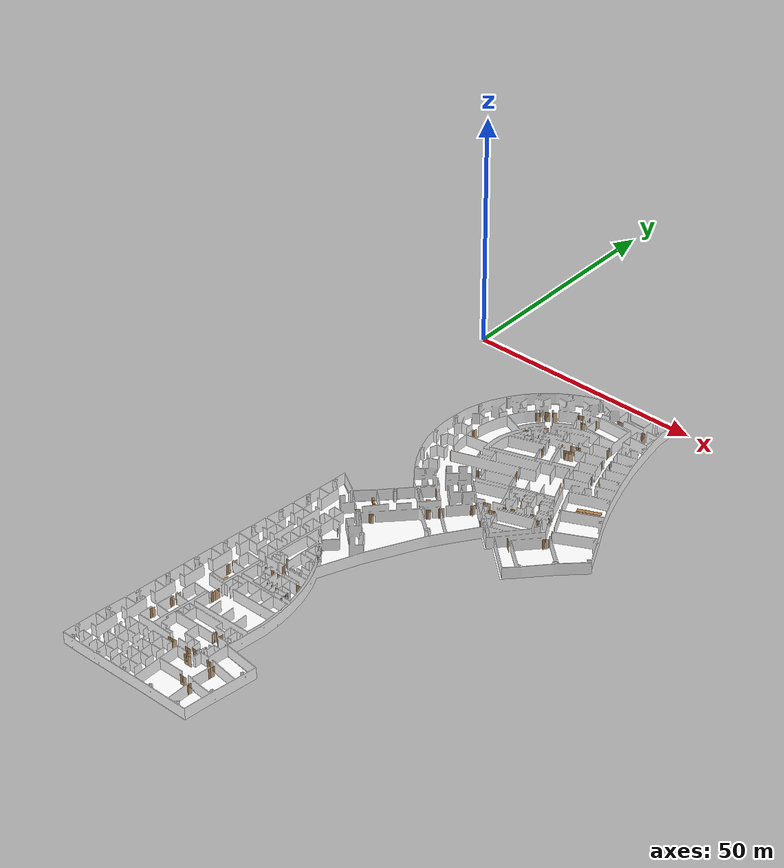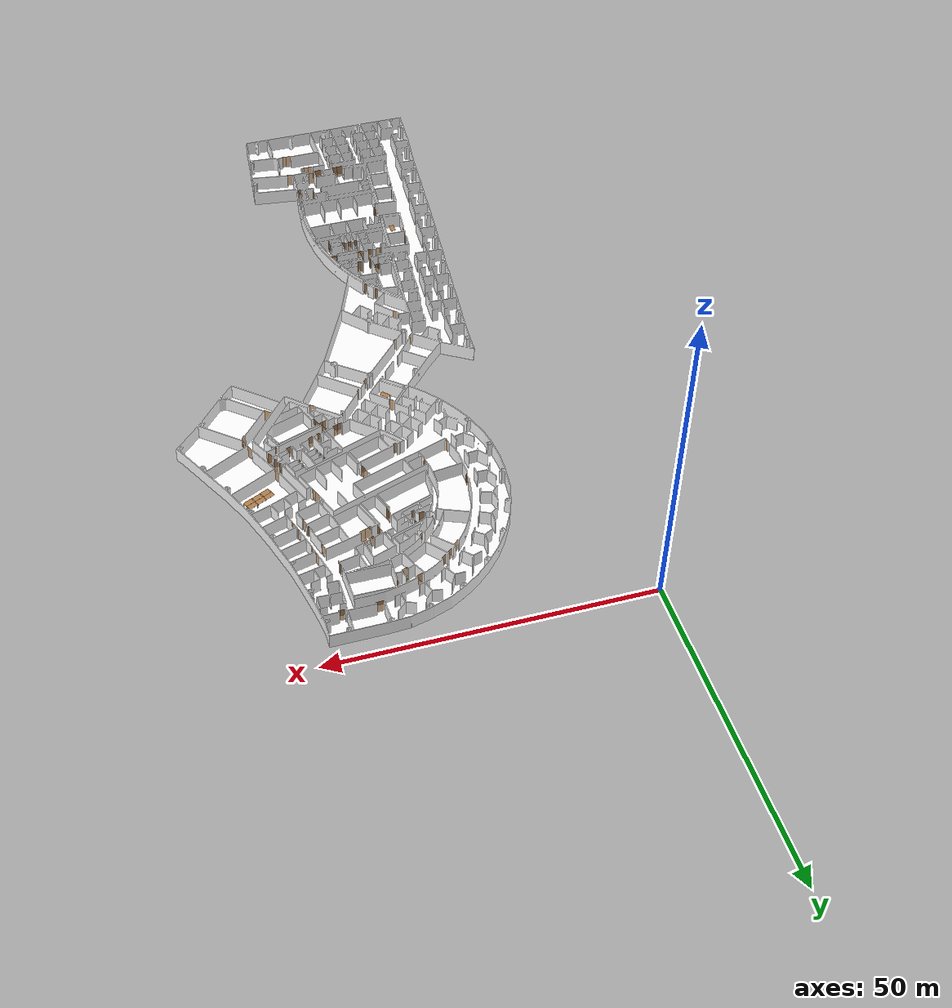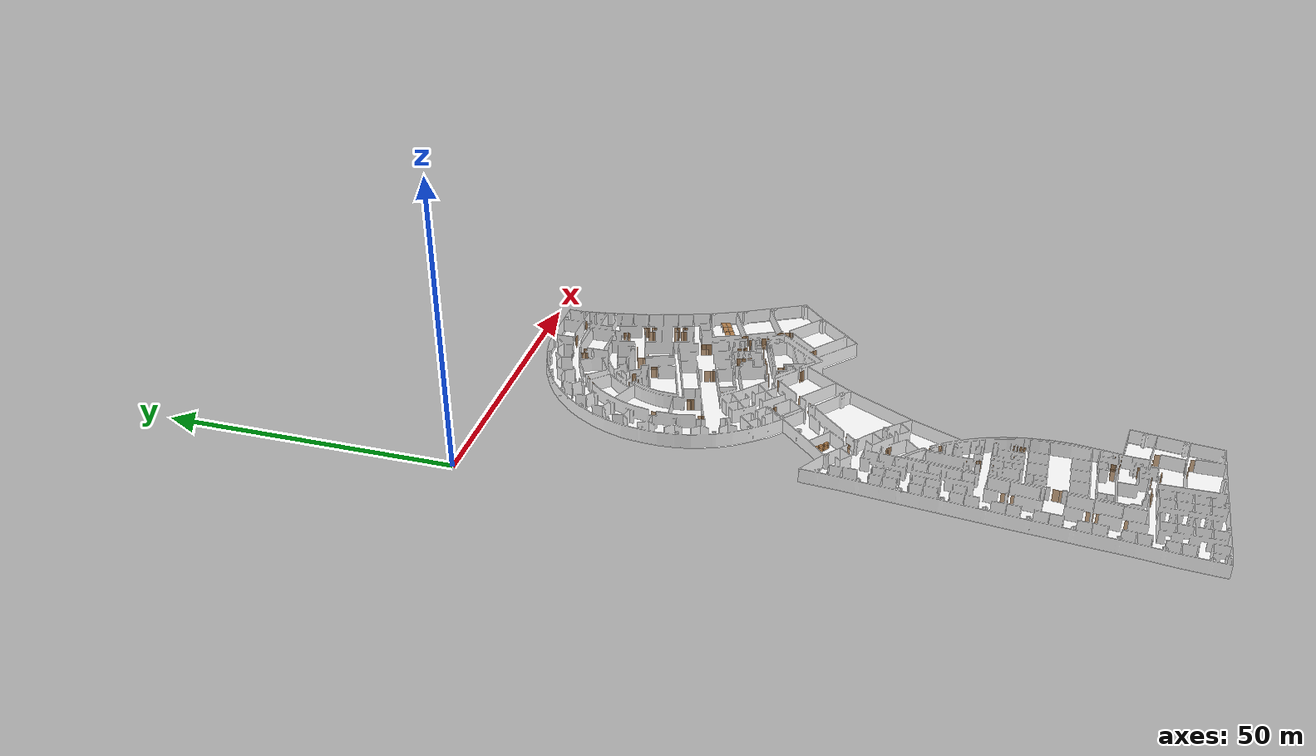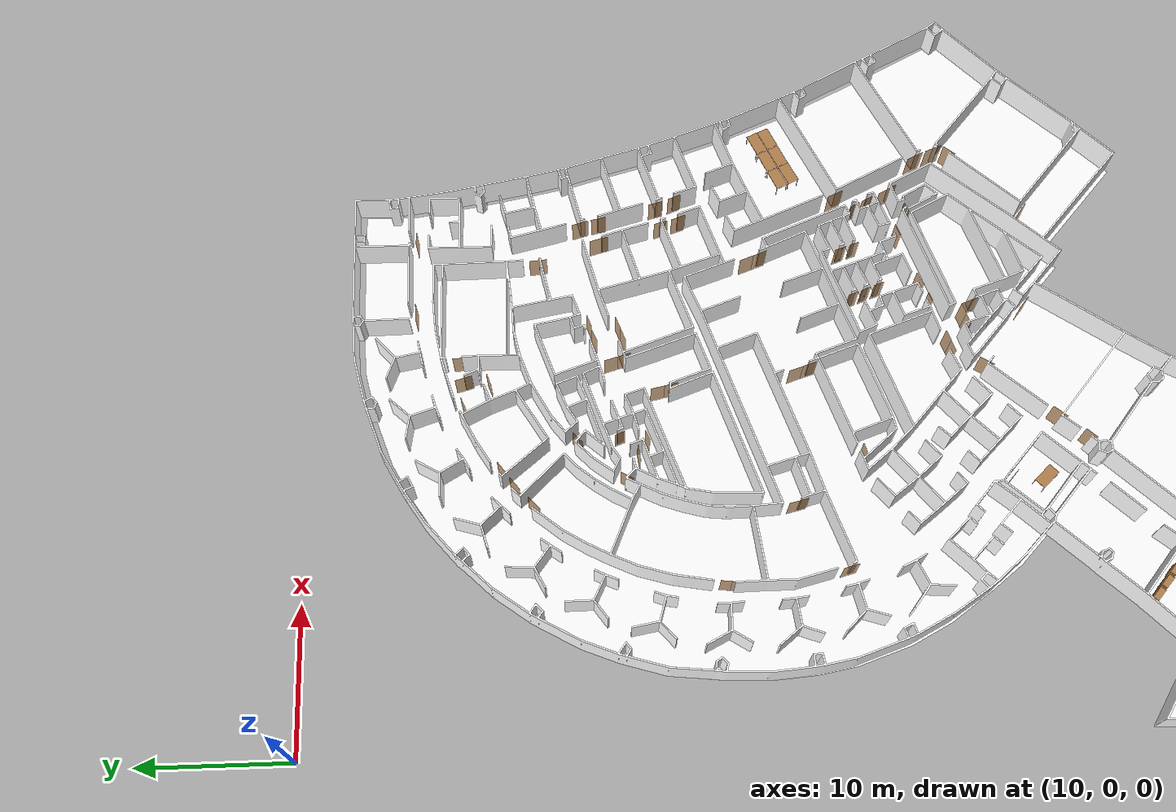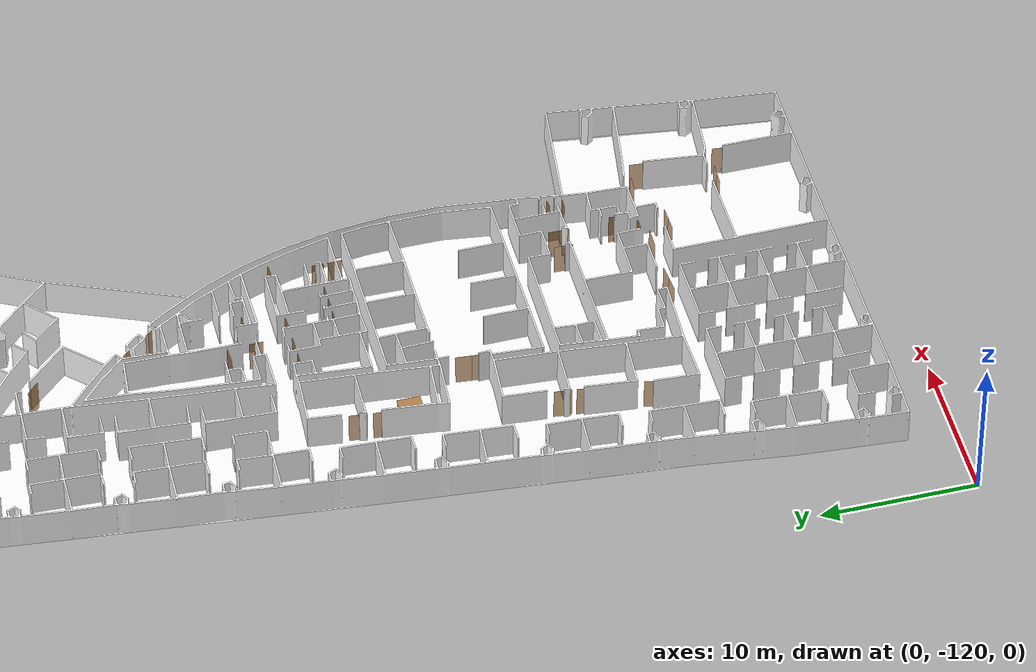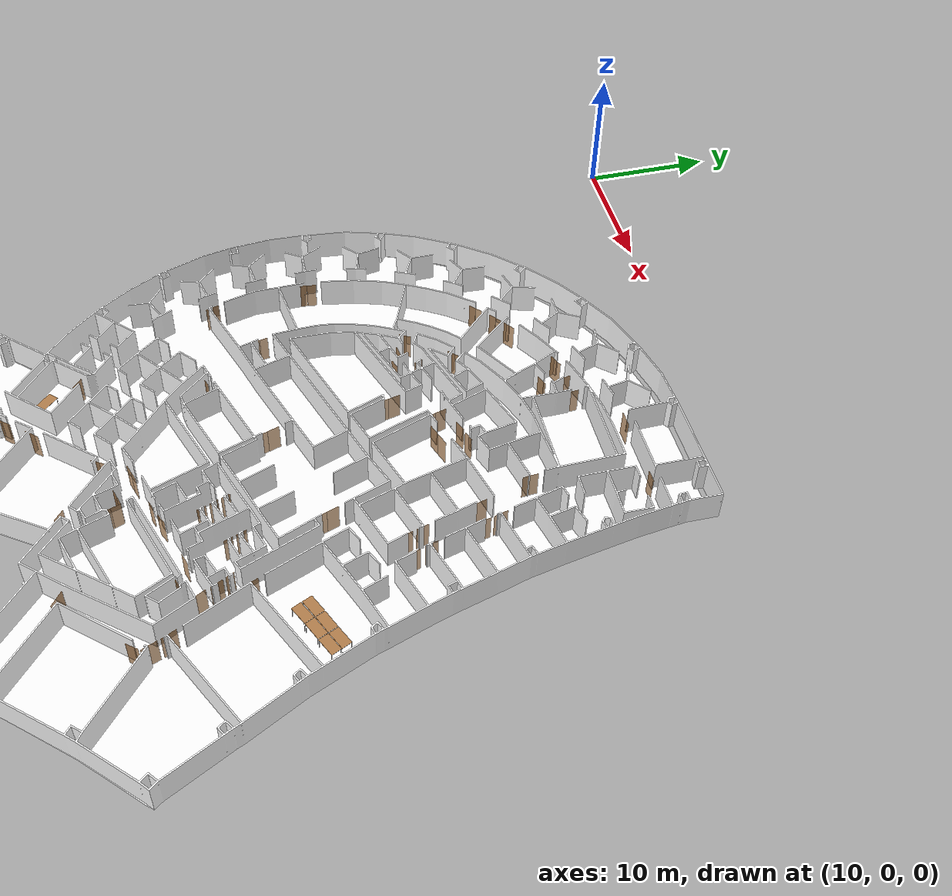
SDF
<sdf version="1.7">
 <world name="world">
  <scene><ambient>0.8 0.8 0.8 1.0</ambient><background>0 0 0</background><grid>false</grid></scene>
  <include><uri>model://sun</uri></include>
  <include>
   <name>OpenRobotics/Table</name>
   <uri>model://Table</uri>
   <pose>14.445396386706355 -88.01514877491877 0.0 0 0 1.5708</pose>
   <static>True</static>
  </include>
  <include>
   <name>OpenRobotics/Table_2</name>
   <uri>model://Table</uri>
   <pose>26.90355624139022 -48.34280959070164 0.0 0 0 2.3292</pose>
   <static>True</static>
  </include>
  <include>
   <name>OpenRobotics/Table_3</name>
   <uri>model://Table</uri>
   <pose>49.315199858933966 -32.279987743199165 0.0 0 0 0.4303</pose>
   <static>True</static>
  </include>
  <include>
   <name>OpenRobotics/Table_4</name>
   <uri>model://Table</uri>
   <pose>50.718865642363795 -31.653960999048657 0.0 0 0 0.4167</pose>
   <static>True</static>
  </include>
  <include>
   <name>OpenRobotics/Table_5</name>
   <uri>model://Table</uri>
   <pose>52.13243403065564 -31.01780400394735 0.0 0 0 0.4347</pose>
   <static>True</static>
  </include>
  <include>
   <name>OpenRobotics/Table_6</name>
   <uri>model://Table</uri>
   <pose>52.47583815558329 -31.77506871828068 0.0 0 0 0.4389</pose>
   <static>True</static>
  </include>
  <include>
   <name>OpenRobotics/Table_7</name>
   <uri>model://Table</uri>
   <pose>51.06215594424706 -32.41122571338198 0.0 0 0 0.4288</pose>
   <static>True</static>
  </include>
  <include>
   <name>OpenRobotics/Table_8</name>
   <uri>model://Table</uri>
   <pose>49.67875066271883 -33.06764321038489 0.0 0 0 0.4547</pose>
   <static>True</static>
  </include>
  <include>
   <name>OpenRobotics/Bookshelf</name>
   <uri>model://Bookshelf</uri>
   <pose>18.97293562344721 -54.263087598610795 0.0 0 0 -0.7204</pose>
   <static>True</static>
  </include>
  <include>
   <name>OpenRobotics/Bookshelf_2</name>
   <uri>model://Bookshelf</uri>
   <pose>19.75956668323342 -54.93134269223036 0.0 0 0 -0.7282</pose>
   <static>True</static>
  </include>
  <include>
   <name>OpenRobotics/Bookshelf_3</name>
   <uri>model://Bookshelf</uri>
   <pose>20.57397056585103 -55.585711374434226 0.0 0 0 -0.7114</pose>
   <static>True</static>
  </include>
  <model name="D1">
   <pose>46.92098903169145 -38.269014869920476 0.0 0 0 -1.0989798712124257</pose>
   <link name="right">
    <pose>0 0 1.11 0 0 0</pose>
    <visual name="right_visual">
     <geometry><box><size>0.9994952973221634 0.03 2.2</size></box></geometry>
     <material><ambient>0.5 0.25 0 0.6</ambient><diffuse>0.5 0.25 0 0.6</diffuse></material>
    </visual>
    <collision name="right_collision">
     <geometry><box><size>0.9994952973221634 0.03 2.2</size></box></geometry>
     <surface><contact><collide_bitmask>0x02</collide_bitmask></contact></surface>
    </collision>
    <inertial>
     <mass>50.0</mass>
     <inertia><ixx>20.17041666666667</ixx><iyy>24.329128539038006</iyy><izz>4.166211872371333</izz></inertia>
    </inertial>
   </link>
   <joint name="right_joint" type="revolute">
    <parent>world</parent>
    <child>right</child>
    <axis><xyz>0 0 1</xyz><limit><lower>0</lower><upper>1.57</upper></limit></axis>
    <pose>0.5047476486610817 0 0 0 0 0</pose>
   </joint>
   <plugin name="door_D1" filename="libdoor.so">
    <v_max_door>0.5</v_max_door>
    <a_max_door>0.3</a_max_door>
    <a_nom_door>0.15</a_nom_door>
    <dx_min_door>0.01</dx_min_door>
    <f_max_door>500.0</f_max_door>
    <door name="D1" type="SwingDoor" left_joint_name="empty_joint" right_joint_name="right_joint"/>
   </plugin>
  </model>
  <model name="D2">
   <pose>40.74187742083717 -41.25282906710838 0.0 0 0 -2.713354953131238</pose>
   <link name="right">
    <pose>0 0 1.11 0 0 0</pose>
    <visual name="right_visual">
     <geometry><box><size>0.9260351120050222 0.03 2.2</size></box></geometry>
     <material><ambient>0.5 0.25 0 0.6</ambient><diffuse>0.5 0.25 0 0.6</diffuse></material>
    </visual>
    <collision name="right_collision">
     <geometry><box><size>0.9260351120050222 0.03 2.2</size></box></geometry>
     <surface><contact><collide_bitmask>0x02</collide_bitmask></contact></surface>
    </collision>
    <inertial>
     <mass>50.0</mass>
     <inertia><ixx>20.17041666666667</ixx><iyy>23.73975428610898</iyy><izz>3.576837619442309</izz></inertia>
    </inertial>
   </link>
   <joint name="right_joint" type="revolute">
    <parent>world</parent>
    <child>right</child>
    <axis><xyz>0 0 1</xyz><limit><lower>0</lower><upper>1.57</upper></limit></axis>
    <pose>0.4680175560025111 0 0 0 0 0</pose>
   </joint>
   <plugin name="door_D2" filename="libdoor.so">
    <v_max_door>0.5</v_max_door>
    <a_max_door>0.3</a_max_door>
    <a_nom_door>0.15</a_nom_door>
    <dx_min_door>0.01</dx_min_door>
    <f_max_door>500.0</f_max_door>
    <door name="D2" type="SwingDoor" left_joint_name="empty_joint" right_joint_name="right_joint"/>
   </plugin>
  </model>
  <model name="D3">
   <pose>44.45780143954799 -40.09541944021848 0.0 0 0 -2.8085231029714666</pose>
   <link name="right">
    <pose>0 0 1.11 0 0 0</pose>
    <visual name="right_visual">
     <geometry><box><size>0.8422487052230405 0.03 2.2</size></box></geometry>
     <material><ambient>0.5 0.25 0 0.6</ambient><diffuse>0.5 0.25 0 0.6</diffuse></material>
    </visual>
    <collision name="right_collision">
     <geometry><box><size>0.8422487052230405 0.03 2.2</size></box></geometry>
     <surface><contact><collide_bitmask>0x02</collide_bitmask></contact></surface>
    </collision>
    <inertial>
     <mass>50.0</mass>
     <inertia><ixx>20.17041666666667</ixx><iyy>23.122428672707873</iyy><izz>2.959512006041201</izz></inertia>
    </inertial>
   </link>
   <joint name="right_joint" type="revolute">
    <parent>world</parent>
    <child>right</child>
    <axis><xyz>0 0 1</xyz><limit><lower>0</lower><upper>1.57</upper></limit></axis>
    <pose>0.42612435261152026 0 0 0 0 0</pose>
   </joint>
   <plugin name="door_D3" filename="libdoor.so">
    <v_max_door>0.5</v_max_door>
    <a_max_door>0.3</a_max_door>
    <a_nom_door>0.15</a_nom_door>
    <dx_min_door>0.01</dx_min_door>
    <f_max_door>500.0</f_max_door>
    <door name="D3" type="SwingDoor" left_joint_name="empty_joint" right_joint_name="right_joint"/>
   </plugin>
  </model>
  <model name="D4">
   <pose>46.452834850111266 -37.32451124756395 0.0 0 0 -1.096903326789822</pose>
   <link name="right">
    <pose>0 0 1.11 0 0 0</pose>
    <visual name="right_visual">
     <geometry><box><size>0.6756513604164147 0.03 2.2</size></box></geometry>
     <material><ambient>0.5 0.25 0 0.6</ambient><diffuse>0.5 0.25 0 0.6</diffuse></material>
    </visual>
    <collision name="right_collision">
     <geometry><box><size>0.6756513604164147 0.03 2.2</size></box></geometry>
     <surface><contact><collide_bitmask>0x02</collide_bitmask></contact></surface>
    </collision>
    <inertial>
     <mass>50.0</mass>
     <inertia><ixx>20.17041666666667</ixx><iyy>22.068769836802307</iyy><izz>1.9058531701356332</izz></inertia>
    </inertial>
   </link>
   <joint name="right_joint" type="revolute">
    <parent>world</parent>
    <child>right</child>
    <axis><xyz>0 0 1</xyz><limit><lower>0</lower><upper>1.57</upper></limit></axis>
    <pose>0.34282568020820736 0 0 0 0 0</pose>
   </joint>
   <plugin name="door_D4" filename="libdoor.so">
    <v_max_door>0.5</v_max_door>
    <a_max_door>0.3</a_max_door>
    <a_nom_door>0.15</a_nom_door>
    <dx_min_door>0.01</dx_min_door>
    <f_max_door>500.0</f_max_door>
    <door name="D4" type="SwingDoor" left_joint_name="empty_joint" right_joint_name="right_joint"/>
   </plugin>
  </model>
  <model name="D5">
   <pose>47.334678886530554 -36.035351446791466 0.0 0 0 -1.15391151212805</pose>
   <link name="right">
    <pose>0 0 1.11 0 0 0</pose>
    <visual name="right_visual">
     <geometry><box><size>1.1116058339812642 0.03 2.2</size></box></geometry>
     <material><ambient>0.5 0.25 0 0.6</ambient><diffuse>0.5 0.25 0 0.6</diffuse></material>
    </visual>
    <collision name="right_collision">
     <geometry><box><size>1.1116058339812642 0.03 2.2</size></box></geometry>
     <surface><contact><collide_bitmask>0x02</collide_bitmask></contact></surface>
    </collision>
    <inertial>
     <mass>50.0</mass>
     <inertia><ixx>20.17041666666667</ixx><iyy>25.315281375588263</iyy><izz>5.152364708921591</izz></inertia>
    </inertial>
   </link>
   <joint name="right_joint" type="revolute">
    <parent>world</parent>
    <child>right</child>
    <axis><xyz>0 0 -1</xyz><limit><lower>0</lower><upper>1.57</upper></limit></axis>
    <pose>0.5608029169906321 0 0 0 0 0</pose>
   </joint>
   <plugin name="door_D5" filename="libdoor.so">
    <v_max_door>0.5</v_max_door>
    <a_max_door>0.3</a_max_door>
    <a_nom_door>0.15</a_nom_door>
    <dx_min_door>0.01</dx_min_door>
    <f_max_door>500.0</f_max_door>
    <door name="D5" type="SwingDoor" left_joint_name="empty_joint" right_joint_name="right_joint"/>
   </plugin>
  </model>
  <model name="D6">
   <pose>50.13620547812626 -41.8280907334605 0.0 0 0 -1.1319738374537602</pose>
   <link name="right">
    <pose>0 0 1.11 0 0 0</pose>
    <visual name="right_visual">
     <geometry><box><size>1.1896493416000884 0.03 2.2</size></box></geometry>
     <material><ambient>0.5 0.25 0 0.6</ambient><diffuse>0.5 0.25 0 0.6</diffuse></material>
    </visual>
    <collision name="right_collision">
     <geometry><box><size>1.1896493416000884 0.03 2.2</size></box></geometry>
     <surface><contact><collide_bitmask>0x02</collide_bitmask></contact></surface>
    </collision>
    <inertial>
     <mass>50.0</mass>
     <inertia><ixx>20.17041666666667</ixx><iyy>26.063606483206353</iyy><izz>5.900689816539682</izz></inertia>
    </inertial>
   </link>
   <joint name="right_joint" type="revolute">
    <parent>world</parent>
    <child>right</child>
    <axis><xyz>0 0 -1</xyz><limit><lower>0</lower><upper>1.57</upper></limit></axis>
    <pose>0.5998246708000442 0 0 0 0 0</pose>
   </joint>
   <plugin name="door_D6" filename="libdoor.so">
    <v_max_door>0.5</v_max_door>
    <a_max_door>0.3</a_max_door>
    <a_nom_door>0.15</a_nom_door>
    <dx_min_door>0.01</dx_min_door>
    <f_max_door>500.0</f_max_door>
    <door name="D6" type="SwingDoor" left_joint_name="empty_joint" right_joint_name="right_joint"/>
   </plugin>
  </model>
  <model name="D7">
   <pose>50.69883278655098 -43.158454476302516 0.0 0 0 -1.1821076421310188</pose>
   <link name="right">
    <pose>0 0 1.11 0 0 0</pose>
    <visual name="right_visual">
     <geometry><box><size>1.2196094655429661 0.03 2.2</size></box></geometry>
     <material><ambient>0.5 0.25 0 0.6</ambient><diffuse>0.5 0.25 0 0.6</diffuse></material>
    </visual>
    <collision name="right_collision">
     <geometry><box><size>1.2196094655429661 0.03 2.2</size></box></geometry>
     <surface><contact><collide_bitmask>0x02</collide_bitmask></contact></surface>
    </collision>
    <inertial>
     <mass>50.0</mass>
     <inertia><ixx>20.17041666666667</ixx><iyy>26.364363535175006</iyy><izz>6.201446868508331</izz></inertia>
    </inertial>
   </link>
   <joint name="right_joint" type="revolute">
    <parent>world</parent>
    <child>right</child>
    <axis><xyz>0 0 1</xyz><limit><lower>0</lower><upper>1.57</upper></limit></axis>
    <pose>0.6148047327714831 0 0 0 0 0</pose>
   </joint>
   <plugin name="door_D7" filename="libdoor.so">
    <v_max_door>0.5</v_max_door>
    <a_max_door>0.3</a_max_door>
    <a_nom_door>0.15</a_nom_door>
    <dx_min_door>0.01</dx_min_door>
    <f_max_door>500.0</f_max_door>
    <door name="D7" type="SwingDoor" left_joint_name="empty_joint" right_joint_name="right_joint"/>
   </plugin>
  </model>
  <model name="D8">
   <pose>50.51688665009196 -44.23738311408482 0.0 0 0 0.8936867215143771</pose>
   <link name="right">
    <pose>0 0 1.11 0 0 0</pose>
    <visual name="right_visual">
     <geometry><box><size>0.958110875327343 0.03 2.2</size></box></geometry>
     <material><ambient>0.5 0.25 0 0.6</ambient><diffuse>0.5 0.25 0 0.6</diffuse></material>
    </visual>
    <collision name="right_collision">
     <geometry><box><size>0.958110875327343 0.03 2.2</size></box></geometry>
     <surface><contact><collide_bitmask>0x02</collide_bitmask></contact></surface>
    </collision>
    <inertial>
     <mass>50.0</mass>
     <inertia><ixx>20.17041666666667</ixx><iyy>23.991568539252203</iyy><izz>3.828651872585531</izz></inertia>
    </inertial>
   </link>
   <joint name="right_joint" type="revolute">
    <parent>world</parent>
    <child>right</child>
    <axis><xyz>0 0 1</xyz><limit><lower>0</lower><upper>1.57</upper></limit></axis>
    <pose>0.4840554376636715 0 0 0 0 0</pose>
   </joint>
   <plugin name="door_D8" filename="libdoor.so">
    <v_max_door>0.5</v_max_door>
    <a_max_door>0.3</a_max_door>
    <a_nom_door>0.15</a_nom_door>
    <dx_min_door>0.01</dx_min_door>
    <f_max_door>500.0</f_max_door>
    <door name="D8" type="SwingDoor" left_joint_name="empty_joint" right_joint_name="right_joint"/>
   </plugin>
  </model>
  <model name="D9">
   <pose>45.727838968862784 -48.67079069311431 0.0 0 0 2.500232906125345</pose>
   <link name="right">
    <pose>0 0 1.11 0 0 0</pose>
    <visual name="right_visual">
     <geometry><box><size>1.3082332286407923 0.03 2.2</size></box></geometry>
     <material><ambient>0.5 0.25 0 0.6</ambient><diffuse>0.5 0.25 0 0.6</diffuse></material>
    </visual>
    <collision name="right_collision">
     <geometry><box><size>1.3082332286407923 0.03 2.2</size></box></geometry>
     <surface><contact><collide_bitmask>0x02</collide_bitmask></contact></surface>
    </collision>
    <inertial>
     <mass>50.0</mass>
     <inertia><ixx>20.17041666666667</ixx><iyy>27.297809085499637</iyy><izz>7.1348924188329645</izz></inertia>
    </inertial>
   </link>
   <joint name="right_joint" type="revolute">
    <parent>world</parent>
    <child>right</child>
    <axis><xyz>0 0 -1</xyz><limit><lower>0</lower><upper>1.57</upper></limit></axis>
    <pose>0.6591166143203961 0 0 0 0 0</pose>
   </joint>
   <plugin name="door_D9" filename="libdoor.so">
    <v_max_door>0.5</v_max_door>
    <a_max_door>0.3</a_max_door>
    <a_nom_door>0.15</a_nom_door>
    <dx_min_door>0.01</dx_min_door>
    <f_max_door>500.0</f_max_door>
    <door name="D9" type="SwingDoor" left_joint_name="empty_joint" right_joint_name="right_joint"/>
   </plugin>
  </model>
  <model name="D10">
   <pose>47.57296742996311 -39.65833894975704 0.0 0 0 -1.079641047657816</pose>
   <link name="right">
    <pose>0 0 1.11 0 0 0</pose>
    <visual name="right_visual">
     <geometry><box><size>1.3928633332641263 0.03 2.2</size></box></geometry>
     <material><ambient>0.5 0.25 0 0.6</ambient><diffuse>0.5 0.25 0 0.6</diffuse></material>
    </visual>
    <collision name="right_collision">
     <geometry><box><size>1.3928633332641263 0.03 2.2</size></box></geometry>
     <surface><contact><collide_bitmask>0x02</collide_bitmask></contact></surface>
    </collision>
    <inertial>
     <mass>50.0</mass>
     <inertia><ixx>20.17041666666667</ixx><iyy>28.250284438131892</iyy><izz>8.08736777146522</izz></inertia>
    </inertial>
   </link>
   <joint name="right_joint" type="revolute">
    <parent>world</parent>
    <child>right</child>
    <axis><xyz>0 0 1</xyz><limit><lower>0</lower><upper>1.57</upper></limit></axis>
    <pose>0.7014316666320631 0 0 0 0 0</pose>
   </joint>
   <plugin name="door_D10" filename="libdoor.so">
    <v_max_door>0.5</v_max_door>
    <a_max_door>0.3</a_max_door>
    <a_nom_door>0.15</a_nom_door>
    <dx_min_door>0.01</dx_min_door>
    <f_max_door>500.0</f_max_door>
    <door name="D10" type="SwingDoor" left_joint_name="empty_joint" right_joint_name="right_joint"/>
   </plugin>
  </model>
  <model name="D11">
   <pose>46.17590338310796 -40.836919662903654 0.0 0 0 0.3930652923323702</pose>
   <link name="right">
    <pose>0 0 1.11 0 0 0</pose>
    <visual name="right_visual">
     <geometry><box><size>0.695187343908026 0.03 2.2</size></box></geometry>
     <material><ambient>0.5 0.25 0 0.6</ambient><diffuse>0.5 0.25 0 0.6</diffuse></material>
    </visual>
    <collision name="right_collision">
     <geometry><box><size>0.695187343908026 0.03 2.2</size></box></geometry>
     <surface><contact><collide_bitmask>0x02</collide_bitmask></contact></surface>
    </collision>
    <inertial>
     <mass>50.0</mass>
     <inertia><ixx>20.17041666666667</ixx><iyy>22.180356013041237</iyy><izz>2.017439346374567</izz></inertia>
    </inertial>
   </link>
   <joint name="right_joint" type="revolute">
    <parent>world</parent>
    <child>right</child>
    <axis><xyz>0 0 1</xyz><limit><lower>0</lower><upper>1.57</upper></limit></axis>
    <pose>0.352593671954013 0 0 0 0 0</pose>
   </joint>
   <plugin name="door_D11" filename="libdoor.so">
    <v_max_door>0.5</v_max_door>
    <a_max_door>0.3</a_max_door>
    <a_nom_door>0.15</a_nom_door>
    <dx_min_door>0.01</dx_min_door>
    <f_max_door>500.0</f_max_door>
    <door name="D11" type="SwingDoor" left_joint_name="empty_joint" right_joint_name="right_joint"/>
   </plugin>
  </model>
  <model name="D12">
   <pose>47.4111679723613 -24.929295536428306 0.0 0 0 -1.2067744343242672</pose>
   <link name="right">
    <pose>0 0 1.11 0 0 0</pose>
    <visual name="right_visual">
     <geometry><box><size>0.9337420534150855 0.03 2.2</size></box></geometry>
     <material><ambient>0.5 0.25 0 0.6</ambient><diffuse>0.5 0.25 0 0.6</diffuse></material>
    </visual>
    <collision name="right_collision">
     <geometry><box><size>0.9337420534150855 0.03 2.2</size></box></geometry>
     <surface><contact><collide_bitmask>0x02</collide_bitmask></contact></surface>
    </collision>
    <inertial>
     <mass>50.0</mass>
     <inertia><ixx>20.17041666666667</ixx><iyy>23.79947592631592</iyy><izz>3.6365592596492524</izz></inertia>
    </inertial>
   </link>
   <joint name="right_joint" type="revolute">
    <parent>world</parent>
    <child>right</child>
    <axis><xyz>0 0 1</xyz><limit><lower>0</lower><upper>1.57</upper></limit></axis>
    <pose>0.4718710267075428 0 0 0 0 0</pose>
   </joint>
   <plugin name="door_D12" filename="libdoor.so">
    <v_max_door>0.5</v_max_door>
    <a_max_door>0.3</a_max_door>
    <a_nom_door>0.15</a_nom_door>
    <dx_min_door>0.01</dx_min_door>
    <f_max_door>500.0</f_max_door>
    <door name="D12" type="SwingDoor" left_joint_name="empty_joint" right_joint_name="right_joint"/>
   </plugin>
  </model>
  <model name="D13">
   <pose>46.973233809066926 -23.635184433224815 0.0 0 0 -1.3188596632420089</pose>
   <link name="right">
    <pose>0 0 1.11 0 0 0</pose>
    <visual name="right_visual">
     <geometry><box><size>0.985860510775004 0.03 2.2</size></box></geometry>
     <material><ambient>0.5 0.25 0 0.6</ambient><diffuse>0.5 0.25 0 0.6</diffuse></material>
    </visual>
    <collision name="right_collision">
     <geometry><box><size>0.985860510775004 0.03 2.2</size></box></geometry>
     <surface><contact><collide_bitmask>0x02</collide_bitmask></contact></surface>
    </collision>
    <inertial>
     <mass>50.0</mass>
     <inertia><ixx>20.17041666666667</ixx><iyy>24.216337277939804</iyy><izz>4.0534206112731335</izz></inertia>
    </inertial>
   </link>
   <joint name="right_joint" type="revolute">
    <parent>world</parent>
    <child>right</child>
    <axis><xyz>0 0 -1</xyz><limit><lower>0</lower><upper>1.57</upper></limit></axis>
    <pose>0.497930255387502 0 0 0 0 0</pose>
   </joint>
   <plugin name="door_D13" filename="libdoor.so">
    <v_max_door>0.5</v_max_door>
    <a_max_door>0.3</a_max_door>
    <a_nom_door>0.15</a_nom_door>
    <dx_min_door>0.01</dx_min_door>
    <f_max_door>500.0</f_max_door>
    <door name="D13" type="SwingDoor" left_joint_name="empty_joint" right_joint_name="right_joint"/>
   </plugin>
  </model>
  <model name="D14">
   <pose>45.88867093058727 -19.64619893101998 0.0 0 0 -1.3543970765350073</pose>
   <link name="right">
    <pose>0 0 1.11 0 0 0</pose>
    <visual name="right_visual">
     <geometry><box><size>0.9908553430227147 0.03 2.2</size></box></geometry>
     <material><ambient>0.5 0.25 0 0.6</ambient><diffuse>0.5 0.25 0 0.6</diffuse></material>
    </visual>
    <collision name="right_collision">
     <geometry><box><size>0.9908553430227147 0.03 2.2</size></box></geometry>
     <surface><contact><collide_bitmask>0x02</collide_bitmask></contact></surface>
    </collision>
    <inertial>
     <mass>50.0</mass>
     <inertia><ixx>20.17041666666667</ixx><iyy>24.2574762949861</iyy><izz>4.094559628319424</izz></inertia>
    </inertial>
   </link>
   <joint name="right_joint" type="revolute">
    <parent>world</parent>
    <child>right</child>
    <axis><xyz>0 0 1</xyz><limit><lower>0</lower><upper>1.57</upper></limit></axis>
    <pose>0.5004276715113574 0 0 0 0 0</pose>
   </joint>
   <plugin name="door_D14" filename="libdoor.so">
    <v_max_door>0.5</v_max_door>
    <a_max_door>0.3</a_max_door>
    <a_nom_door>0.15</a_nom_door>
    <dx_min_door>0.01</dx_min_door>
    <f_max_door>500.0</f_max_door>
    <door name="D14" type="SwingDoor" left_joint_name="empty_joint" right_joint_name="right_joint"/>
   </plugin>
  </model>
  <model name="D15">
   <pose>45.58960088144991 -18.396364992084592 0.0 0 0 -1.296644167364205</pose>
   <link name="right">
    <pose>0 0 1.11 0 0 0</pose>
    <visual name="right_visual">
     <geometry><box><size>1.1096018485833443 0.03 2.2</size></box></geometry>
     <material><ambient>0.5 0.25 0 0.6</ambient><diffuse>0.5 0.25 0 0.6</diffuse></material>
    </visual>
    <collision name="right_collision">
     <geometry><box><size>1.1096018485833443 0.03 2.2</size></box></geometry>
     <surface><contact><collide_bitmask>0x02</collide_bitmask></contact></surface>
    </collision>
    <inertial>
     <mass>50.0</mass>
     <inertia><ixx>20.17041666666667</ixx><iyy>25.296734426581565</iyy><izz>5.133817759914896</izz></inertia>
    </inertial>
   </link>
   <joint name="right_joint" type="revolute">
    <parent>world</parent>
    <child>right</child>
    <axis><xyz>0 0 -1</xyz><limit><lower>0</lower><upper>1.57</upper></limit></axis>
    <pose>0.5598009242916722 0 0 0 0 0</pose>
   </joint>
   <plugin name="door_D15" filename="libdoor.so">
    <v_max_door>0.5</v_max_door>
    <a_max_door>0.3</a_max_door>
    <a_nom_door>0.15</a_nom_door>
    <dx_min_door>0.01</dx_min_door>
    <f_max_door>500.0</f_max_door>
    <door name="D15" type="SwingDoor" left_joint_name="empty_joint" right_joint_name="right_joint"/>
   </plugin>
  </model>
  <model name="D16">
   <pose>42.83855481004161 -15.480446240875924 0.0 0 0 -1.4795248715580727</pose>
   <link name="right">
    <pose>0 0 1.11 0 0 0</pose>
    <visual name="right_visual">
     <geometry><box><size>1.1863654958117862 0.03 2.2</size></box></geometry>
     <material><ambient>0.5 0.25 0 0.6</ambient><diffuse>0.5 0.25 0 0.6</diffuse></material>
    </visual>
    <collision name="right_collision">
     <geometry><box><size>1.1863654958117862 0.03 2.2</size></box></geometry>
     <surface><contact><collide_bitmask>0x02</collide_bitmask></contact></surface>
    </collision>
    <inertial>
     <mass>50.0</mass>
     <inertia><ixx>20.17041666666667</ixx><iyy>26.031096206886446</iyy><izz>5.8681795402197725</izz></inertia>
    </inertial>
   </link>
   <joint name="right_joint" type="revolute">
    <parent>world</parent>
    <child>right</child>
    <axis><xyz>0 0 1</xyz><limit><lower>0</lower><upper>1.57</upper></limit></axis>
    <pose>0.5981827479058931 0 0 0 0 0</pose>
   </joint>
   <plugin name="door_D16" filename="libdoor.so">
    <v_max_door>0.5</v_max_door>
    <a_max_door>0.3</a_max_door>
    <a_nom_door>0.15</a_nom_door>
    <dx_min_door>0.01</dx_min_door>
    <f_max_door>500.0</f_max_door>
    <door name="D16" type="SwingDoor" left_joint_name="empty_joint" right_joint_name="right_joint"/>
   </plugin>
  </model>
  <model name="D17">
   <pose>44.32724640763151 -19.63549956484723 0.0 0 0 1.8422869865588756</pose>
   <link name="right">
    <pose>0 0 1.11 0 0 0</pose>
    <visual name="right_visual">
     <geometry><box><size>1.2896570405738117 0.03 2.2</size></box></geometry>
     <material><ambient>0.5 0.25 0 0.6</ambient><diffuse>0.5 0.25 0 0.6</diffuse></material>
    </visual>
    <collision name="right_collision">
     <geometry><box><size>1.2896570405738117 0.03 2.2</size></box></geometry>
     <surface><contact><collide_bitmask>0x02</collide_bitmask></contact></surface>
    </collision>
    <inertial>
     <mass>50.0</mass>
     <inertia><ixx>20.17041666666667</ixx><iyy>27.09673034292335</iyy><izz>6.933813676256676</izz></inertia>
    </inertial>
   </link>
   <joint name="right_joint" type="revolute">
    <parent>world</parent>
    <child>right</child>
    <axis><xyz>0 0 -1</xyz><limit><lower>0</lower><upper>1.57</upper></limit></axis>
    <pose>0.6498285202869059 0 0 0 0 0</pose>
   </joint>
   <plugin name="door_D17" filename="libdoor.so">
    <v_max_door>0.5</v_max_door>
    <a_max_door>0.3</a_max_door>
    <a_nom_door>0.15</a_nom_door>
    <dx_min_door>0.01</dx_min_door>
    <f_max_door>500.0</f_max_door>
    <door name="D17" type="SwingDoor" left_joint_name="empty_joint" right_joint_name="right_joint"/>
   </plugin>
  </model>
  <model name="D18">
   <pose>45.47509489879256 -23.926116134688215 0.0 0 0 1.8423285281827253</pose>
   <link name="right">
    <pose>0 0 1.11 0 0 0</pose>
    <visual name="right_visual">
     <geometry><box><size>0.9580193886466375 0.03 2.2</size></box></geometry>
     <material><ambient>0.5 0.25 0 0.6</ambient><diffuse>0.5 0.25 0 0.6</diffuse></material>
    </visual>
    <collision name="right_collision">
     <geometry><box><size>0.9580193886466375 0.03 2.2</size></box></geometry>
     <surface><contact><collide_bitmask>0x02</collide_bitmask></contact></surface>
    </collision>
    <inertial>
     <mass>50.0</mass>
     <inertia><ixx>20.17041666666667</ixx><iyy>23.99083812092866</iyy><izz>3.827921454261988</izz></inertia>
    </inertial>
   </link>
   <joint name="right_joint" type="revolute">
    <parent>world</parent>
    <child>right</child>
    <axis><xyz>0 0 1</xyz><limit><lower>0</lower><upper>1.57</upper></limit></axis>
    <pose>0.48400969432331875 0 0 0 0 0</pose>
   </joint>
   <plugin name="door_D18" filename="libdoor.so">
    <v_max_door>0.5</v_max_door>
    <a_max_door>0.3</a_max_door>
    <a_nom_door>0.15</a_nom_door>
    <dx_min_door>0.01</dx_min_door>
    <f_max_door>500.0</f_max_door>
    <door name="D18" type="SwingDoor" left_joint_name="empty_joint" right_joint_name="right_joint"/>
   </plugin>
  </model>
  <model name="D19">
   <pose>45.829995151203704 -25.132697316755024 0.0 0 0 1.9038844260786403</pose>
   <link name="right">
    <pose>0 0 1.11 0 0 0</pose>
    <visual name="right_visual">
     <geometry><box><size>0.9964211250376829 0.03 2.2</size></box></geometry>
     <material><ambient>0.5 0.25 0 0.6</ambient><diffuse>0.5 0.25 0 0.6</diffuse></material>
    </visual>
    <collision name="right_collision">
     <geometry><box><size>0.9964211250376829 0.03 2.2</size></box></geometry>
     <surface><contact><collide_bitmask>0x02</collide_bitmask></contact></surface>
    </collision>
    <inertial>
     <mass>50.0</mass>
     <inertia><ixx>20.17041666666667</ixx><iyy>24.303562743422344</iyy><izz>4.140646076755674</izz></inertia>
    </inertial>
   </link>
   <joint name="right_joint" type="revolute">
    <parent>world</parent>
    <child>right</child>
    <axis><xyz>0 0 -1</xyz><limit><lower>0</lower><upper>1.57</upper></limit></axis>
    <pose>0.5032105625188414 0 0 0 0 0</pose>
   </joint>
   <plugin name="door_D19" filename="libdoor.so">
    <v_max_door>0.5</v_max_door>
    <a_max_door>0.3</a_max_door>
    <a_nom_door>0.15</a_nom_door>
    <dx_min_door>0.01</dx_min_door>
    <f_max_door>500.0</f_max_door>
    <door name="D19" type="SwingDoor" left_joint_name="empty_joint" right_joint_name="right_joint"/>
   </plugin>
  </model>
  <model name="D20">
   <pose>40.43922194580149 -38.43462739950938 0.0 0 0 -1.225222611764381</pose>
   <link name="right">
    <pose>0 0 1.11 0 0 0</pose>
    <visual name="right_visual">
     <geometry><box><size>0.6986711318985143 0.03 2.2</size></box></geometry>
     <material><ambient>0.5 0.25 0 0.6</ambient><diffuse>0.5 0.25 0 0.6</diffuse></material>
    </visual>
    <collision name="right_collision">
     <geometry><box><size>0.6986711318985143 0.03 2.2</size></box></geometry>
     <surface><contact><collide_bitmask>0x02</collide_bitmask></contact></surface>
    </collision>
    <inertial>
     <mass>50.0</mass>
     <inertia><ixx>20.17041666666667</ixx><iyy>22.200588960618134</iyy><izz>2.0376722939514633</izz></inertia>
    </inertial>
   </link>
   <joint name="right_joint" type="revolute">
    <parent>world</parent>
    <child>right</child>
    <axis><xyz>0 0 1</xyz><limit><lower>0</lower><upper>1.57</upper></limit></axis>
    <pose>0.35433556594925714 0 0 0 0 0</pose>
   </joint>
   <plugin name="door_D20" filename="libdoor.so">
    <v_max_door>0.5</v_max_door>
    <a_max_door>0.3</a_max_door>
    <a_nom_door>0.15</a_nom_door>
    <dx_min_door>0.01</dx_min_door>
    <f_max_door>500.0</f_max_door>
    <door name="D20" type="SwingDoor" left_joint_name="empty_joint" right_joint_name="right_joint"/>
   </plugin>
  </model>
  <model name="D21">
   <pose>40.099687804383144 -37.52444142503674 0.0 0 0 -1.173716881569916</pose>
   <link name="right">
    <pose>0 0 1.11 0 0 0</pose>
    <visual name="right_visual">
     <geometry><box><size>0.6825449934010345 0.03 2.2</size></box></geometry>
     <material><ambient>0.5 0.25 0 0.6</ambient><diffuse>0.5 0.25 0 0.6</diffuse></material>
    </visual>
    <collision name="right_collision">
     <geometry><box><size>0.6825449934010345 0.03 2.2</size></box></geometry>
     <surface><contact><collide_bitmask>0x02</collide_bitmask></contact></surface>
    </collision>
    <inertial>
     <mass>50.0</mass>
     <inertia><ixx>20.17041666666667</ixx><iyy>22.10778195007008</iyy><izz>1.9448652834034093</izz></inertia>
    </inertial>
   </link>
   <joint name="right_joint" type="revolute">
    <parent>world</parent>
    <child>right</child>
    <axis><xyz>0 0 1</xyz><limit><lower>0</lower><upper>1.57</upper></limit></axis>
    <pose>0.34627249670051724 0 0 0 0 0</pose>
   </joint>
   <plugin name="door_D21" filename="libdoor.so">
    <v_max_door>0.5</v_max_door>
    <a_max_door>0.3</a_max_door>
    <a_nom_door>0.15</a_nom_door>
    <dx_min_door>0.01</dx_min_door>
    <f_max_door>500.0</f_max_door>
    <door name="D21" type="SwingDoor" left_joint_name="empty_joint" right_joint_name="right_joint"/>
   </plugin>
  </model>
  <model name="D22">
   <pose>39.76795054150557 -36.65284146261264 0.0 0 0 -1.2232855965163554</pose>
   <link name="right">
    <pose>0 0 1.11 0 0 0</pose>
    <visual name="right_visual">
     <geometry><box><size>0.6998933678384069 0.03 2.2</size></box></geometry>
     <material><ambient>0.5 0.25 0 0.6</ambient><diffuse>0.5 0.25 0 0.6</diffuse></material>
    </visual>
    <collision name="right_collision">
     <geometry><box><size>0.6998933678384069 0.03 2.2</size></box></geometry>
     <surface><contact><collide_bitmask>0x02</collide_bitmask></contact></surface>
    </collision>
    <inertial>
     <mass>50.0</mass>
     <inertia><ixx>20.17041666666667</ixx><iyy>22.207711359767455</iyy><izz>2.0447946931007817</izz></inertia>
    </inertial>
   </link>
   <joint name="right_joint" type="revolute">
    <parent>world</parent>
    <child>right</child>
    <axis><xyz>0 0 1</xyz><limit><lower>0</lower><upper>1.57</upper></limit></axis>
    <pose>0.3549466839192035 0 0 0 0 0</pose>
   </joint>
   <plugin name="door_D22" filename="libdoor.so">
    <v_max_door>0.5</v_max_door>
    <a_max_door>0.3</a_max_door>
    <a_nom_door>0.15</a_nom_door>
    <dx_min_door>0.01</dx_min_door>
    <f_max_door>500.0</f_max_door>
    <door name="D22" type="SwingDoor" left_joint_name="empty_joint" right_joint_name="right_joint"/>
   </plugin>
  </model>
  <model name="D23">
   <pose>43.486549401759575 -37.0138881594209 0.0 0 0 -1.2084228363325602</pose>
   <link name="right">
    <pose>0 0 1.11 0 0 0</pose>
    <visual name="right_visual">
     <geometry><box><size>0.6777649873222565 0.03 2.2</size></box></geometry>
     <material><ambient>0.5 0.25 0 0.6</ambient><diffuse>0.5 0.25 0 0.6</diffuse></material>
    </visual>
    <collision name="right_collision">
     <geometry><box><size>0.6777649873222565 0.03 2.2</size></box></geometry>
     <surface><contact><collide_bitmask>0x02</collide_bitmask></contact></surface>
    </collision>
    <inertial>
     <mass>50.0</mass>
     <inertia><ixx>20.17041666666667</ixx><iyy>22.08068907516642</iyy><izz>1.917772408499744</izz></inertia>
    </inertial>
   </link>
   <joint name="right_joint" type="revolute">
    <parent>world</parent>
    <child>right</child>
    <axis><xyz>0 0 1</xyz><limit><lower>0</lower><upper>1.57</upper></limit></axis>
    <pose>0.3438824936611283 0 0 0 0 0</pose>
   </joint>
   <plugin name="door_D23" filename="libdoor.so">
    <v_max_door>0.5</v_max_door>
    <a_max_door>0.3</a_max_door>
    <a_nom_door>0.15</a_nom_door>
    <dx_min_door>0.01</dx_min_door>
    <f_max_door>500.0</f_max_door>
    <door name="D23" type="SwingDoor" left_joint_name="empty_joint" right_joint_name="right_joint"/>
   </plugin>
  </model>
  <model name="D24">
   <pose>43.149007163618066 -36.05532739108209 0.0 0 0 -1.2416042181407194</pose>
   <link name="right">
    <pose>0 0 1.11 0 0 0</pose>
    <visual name="right_visual">
     <geometry><box><size>0.7832578912584792 0.03 2.2</size></box></geometry>
     <material><ambient>0.5 0.25 0 0.6</ambient><diffuse>0.5 0.25 0 0.6</diffuse></material>
    </visual>
    <collision name="right_collision">
     <geometry><box><size>0.7832578912584792 0.03 2.2</size></box></geometry>
     <surface><contact><collide_bitmask>0x02</collide_bitmask></contact></surface>
    </collision>
    <inertial>
     <mass>50.0</mass>
     <inertia><ixx>20.17041666666667</ixx><iyy>22.722887184244502</iyy><izz>2.559970517577832</izz></inertia>
    </inertial>
   </link>
   <joint name="right_joint" type="revolute">
    <parent>world</parent>
    <child>right</child>
    <axis><xyz>0 0 1</xyz><limit><lower>0</lower><upper>1.57</upper></limit></axis>
    <pose>0.3966289456292396 0 0 0 0 0</pose>
   </joint>
   <plugin name="door_D24" filename="libdoor.so">
    <v_max_door>0.5</v_max_door>
    <a_max_door>0.3</a_max_door>
    <a_nom_door>0.15</a_nom_door>
    <dx_min_door>0.01</dx_min_door>
    <f_max_door>500.0</f_max_door>
    <door name="D24" type="SwingDoor" left_joint_name="empty_joint" right_joint_name="right_joint"/>
   </plugin>
  </model>
  <model name="D25">
   <pose>32.5059833978375 -10.474679483126277 0.0 0 0 -2.751995442728913</pose>
   <link name="right">
    <pose>0 0 1.11 0 0 0</pose>
    <visual name="right_visual">
     <geometry><box><size>1.0874265515017651 0.03 2.2</size></box></geometry>
     <material><ambient>0.5 0.25 0 0.6</ambient><diffuse>0.5 0.25 0 0.6</diffuse></material>
    </visual>
    <collision name="right_collision">
     <geometry><box><size>1.0874265515017651 0.03 2.2</size></box></geometry>
     <surface><contact><collide_bitmask>0x02</collide_bitmask></contact></surface>
    </collision>
    <inertial>
     <mass>50.0</mass>
     <inertia><ixx>20.17041666666667</ixx><iyy>25.093735437129258</iyy><izz>4.930818770462587</izz></inertia>
    </inertial>
   </link>
   <joint name="right_joint" type="revolute">
    <parent>world</parent>
    <child>right</child>
    <axis><xyz>0 0 -1</xyz><limit><lower>0</lower><upper>1.57</upper></limit></axis>
    <pose>0.5487132757508826 0 0 0 0 0</pose>
   </joint>
   <plugin name="door_D25" filename="libdoor.so">
    <v_max_door>0.5</v_max_door>
    <a_max_door>0.3</a_max_door>
    <a_nom_door>0.15</a_nom_door>
    <dx_min_door>0.01</dx_min_door>
    <f_max_door>500.0</f_max_door>
    <door name="D25" type="SwingDoor" left_joint_name="empty_joint" right_joint_name="right_joint"/>
   </plugin>
  </model>
  <model name="D26">
   <pose>34.2552159440384 -12.10798325861495 0.0 0 0 -2.8019398110521796</pose>
   <link name="right">
    <pose>0 0 1.11 0 0 0</pose>
    <visual name="right_visual">
     <geometry><box><size>0.9189382125127755 0.03 2.2</size></box></geometry>
     <material><ambient>0.5 0.25 0 0.6</ambient><diffuse>0.5 0.25 0 0.6</diffuse></material>
    </visual>
    <collision name="right_collision">
     <geometry><box><size>0.9189382125127755 0.03 2.2</size></box></geometry>
     <surface><contact><collide_bitmask>0x02</collide_bitmask></contact></surface>
    </collision>
    <inertial>
     <mass>50.0</mass>
     <inertia><ixx>20.17041666666667</ixx><iyy>23.685197660067402</iyy><izz>3.5222809934007295</izz></inertia>
    </inertial>
   </link>
   <joint name="right_joint" type="revolute">
    <parent>world</parent>
    <child>right</child>
    <axis><xyz>0 0 1</xyz><limit><lower>0</lower><upper>1.57</upper></limit></axis>
    <pose>0.46446910625638776 0 0 0 0 0</pose>
   </joint>
   <plugin name="door_D26" filename="libdoor.so">
    <v_max_door>0.5</v_max_door>
    <a_max_door>0.3</a_max_door>
    <a_nom_door>0.15</a_nom_door>
    <dx_min_door>0.01</dx_min_door>
    <f_max_door>500.0</f_max_door>
    <door name="D26" type="SwingDoor" left_joint_name="empty_joint" right_joint_name="right_joint"/>
   </plugin>
  </model>
  <model name="D27">
   <pose>34.38611244508806 -10.436434940210901 0.0 0 0 1.8376123916784604</pose>
   <link name="right">
    <pose>0 0 1.11 0 0 0</pose>
    <visual name="right_visual">
     <geometry><box><size>1.140484263080397 0.03 2.2</size></box></geometry>
     <material><ambient>0.5 0.25 0 0.6</ambient><diffuse>0.5 0.25 0 0.6</diffuse></material>
    </visual>
    <collision name="right_collision">
     <geometry><box><size>1.140484263080397 0.03 2.2</size></box></geometry>
     <surface><contact><collide_bitmask>0x02</collide_bitmask></contact></surface>
    </collision>
    <inertial>
     <mass>50.0</mass>
     <inertia><ixx>20.17041666666667</ixx><iyy>25.58626814305849</iyy><izz>5.423351476391819</izz></inertia>
    </inertial>
   </link>
   <joint name="right_joint" type="revolute">
    <parent>world</parent>
    <child>right</child>
    <axis><xyz>0 0 1</xyz><limit><lower>0</lower><upper>1.57</upper></limit></axis>
    <pose>0.5752421315401985 0 0 0 0 0</pose>
   </joint>
   <plugin name="door_D27" filename="libdoor.so">
    <v_max_door>0.5</v_max_door>
    <a_max_door>0.3</a_max_door>
    <a_nom_door>0.15</a_nom_door>
    <dx_min_door>0.01</dx_min_door>
    <f_max_door>500.0</f_max_door>
    <door name="D27" type="SwingDoor" left_joint_name="empty_joint" right_joint_name="right_joint"/>
   </plugin>
  </model>
  <model name="D28">
   <pose>35.82728292164471 -10.276911943496913 0.0 0 0 1.6268911847432377</pose>
   <link name="right">
    <pose>0 0 1.11 0 0 0</pose>
    <visual name="right_visual">
     <geometry><box><size>1.1228414429880713 0.03 2.2</size></box></geometry>
     <material><ambient>0.5 0.25 0 0.6</ambient><diffuse>0.5 0.25 0 0.6</diffuse></material>
    </visual>
    <collision name="right_collision">
     <geometry><box><size>1.1228414429880713 0.03 2.2</size></box></geometry>
     <surface><contact><collide_bitmask>0x02</collide_bitmask></contact></surface>
    </collision>
    <inertial>
     <mass>50.0</mass>
     <inertia><ixx>20.17041666666667</ixx><iyy>25.419887108714732</iyy><izz>5.256970442048059</izz></inertia>
    </inertial>
   </link>
   <joint name="right_joint" type="revolute">
    <parent>world</parent>
    <child>right</child>
    <axis><xyz>0 0 1</xyz><limit><lower>0</lower><upper>1.57</upper></limit></axis>
    <pose>0.5664207214940357 0 0 0 0 0</pose>
   </joint>
   <plugin name="door_D28" filename="libdoor.so">
    <v_max_door>0.5</v_max_door>
    <a_max_door>0.3</a_max_door>
    <a_nom_door>0.15</a_nom_door>
    <dx_min_door>0.01</dx_min_door>
    <f_max_door>500.0</f_max_door>
    <door name="D28" type="SwingDoor" left_joint_name="empty_joint" right_joint_name="right_joint"/>
   </plugin>
  </model>
  <model name="D29">
   <pose>39.288755524619454 -7.233966674747887 0.0 0 0 -3.118114170019577</pose>
   <link name="right">
    <pose>0 0 1.11 0 0 0</pose>
    <visual name="right_visual">
     <geometry><box><size>1.1681655739603571 0.03 2.2</size></box></geometry>
     <material><ambient>0.5 0.25 0 0.6</ambient><diffuse>0.5 0.25 0 0.6</diffuse></material>
    </visual>
    <collision name="right_collision">
     <geometry><box><size>1.1681655739603571 0.03 2.2</size></box></geometry>
     <surface><contact><collide_bitmask>0x02</collide_bitmask></contact></surface>
    </collision>
    <inertial>
     <mass>50.0</mass>
     <inertia><ixx>20.17041666666667</ixx><iyy>25.852545034108882</iyy><izz>5.689628367442211</izz></inertia>
    </inertial>
   </link>
   <joint name="right_joint" type="revolute">
    <parent>world</parent>
    <child>right</child>
    <axis><xyz>0 0 1</xyz><limit><lower>0</lower><upper>1.57</upper></limit></axis>
    <pose>0.5890827869801786 0 0 0 0 0</pose>
   </joint>
   <plugin name="door_D29" filename="libdoor.so">
    <v_max_door>0.5</v_max_door>
    <a_max_door>0.3</a_max_door>
    <a_nom_door>0.15</a_nom_door>
    <dx_min_door>0.01</dx_min_door>
    <f_max_door>500.0</f_max_door>
    <door name="D29" type="SwingDoor" left_joint_name="empty_joint" right_joint_name="right_joint"/>
   </plugin>
  </model>
  <model name="D30">
   <pose>44.790961490480456 -7.2198526172434025 0.0 0 0 3.1409787047474826</pose>
   <link name="right">
    <pose>0 0 1.11 0 0 0</pose>
    <visual name="right_visual">
     <geometry><box><size>0.9169750482241364 0.03 2.2</size></box></geometry>
     <material><ambient>0.5 0.25 0 0.6</ambient><diffuse>0.5 0.25 0 0.6</diffuse></material>
    </visual>
    <collision name="right_collision">
     <geometry><box><size>0.9169750482241364 0.03 2.2</size></box></geometry>
     <surface><contact><collide_bitmask>0x02</collide_bitmask></contact></surface>
    </collision>
    <inertial>
     <mass>50.0</mass>
     <inertia><ixx>20.17041666666667</ixx><iyy>23.670180162773576</iyy><izz>3.5072634961069062</izz></inertia>
    </inertial>
   </link>
   <joint name="right_joint" type="revolute">
    <parent>world</parent>
    <child>right</child>
    <axis><xyz>0 0 1</xyz><limit><lower>0</lower><upper>1.57</upper></limit></axis>
    <pose>0.4634875241120682 0 0 0 0 0</pose>
   </joint>
   <plugin name="door_D30" filename="libdoor.so">
    <v_max_door>0.5</v_max_door>
    <a_max_door>0.3</a_max_door>
    <a_nom_door>0.15</a_nom_door>
    <dx_min_door>0.01</dx_min_door>
    <f_max_door>500.0</f_max_door>
    <door name="D30" type="SwingDoor" left_joint_name="empty_joint" right_joint_name="right_joint"/>
   </plugin>
  </model>
  <model name="D31">
   <pose>28.087315903056634 -12.94002971311317 0.0 0 0 -2.5071322216960636</pose>
   <link name="right">
    <pose>0 0 1.11 0 0 0</pose>
    <visual name="right_visual">
     <geometry><box><size>1.0375107565587116 0.03 2.2</size></box></geometry>
     <material><ambient>0.5 0.25 0 0.6</ambient><diffuse>0.5 0.25 0 0.6</diffuse></material>
    </visual>
    <collision name="right_collision">
     <geometry><box><size>1.0375107565587116 0.03 2.2</size></box></geometry>
     <surface><contact><collide_bitmask>0x02</collide_bitmask></contact></surface>
    </collision>
    <inertial>
     <mass>50.0</mass>
     <inertia><ixx>20.17041666666667</ixx><iyy>24.651785708229294</iyy><izz>4.488869041562626</izz></inertia>
    </inertial>
   </link>
   <joint name="right_joint" type="revolute">
    <parent>world</parent>
    <child>right</child>
    <axis><xyz>0 0 -1</xyz><limit><lower>0</lower><upper>1.57</upper></limit></axis>
    <pose>0.5237553782793558 0 0 0 0 0</pose>
   </joint>
   <plugin name="door_D31" filename="libdoor.so">
    <v_max_door>0.5</v_max_door>
    <a_max_door>0.3</a_max_door>
    <a_nom_door>0.15</a_nom_door>
    <dx_min_door>0.01</dx_min_door>
    <f_max_door>500.0</f_max_door>
    <door name="D31" type="SwingDoor" left_joint_name="empty_joint" right_joint_name="right_joint"/>
   </plugin>
  </model>
  <model name="D32">
   <pose>27.046404162100927 -13.721481824379588 0.0 0 0 -2.4843833079863797</pose>
   <link name="right">
    <pose>0 0 1.11 0 0 0</pose>
    <visual name="right_visual">
     <geometry><box><size>1.0628146973727688 0.03 2.2</size></box></geometry>
     <material><ambient>0.5 0.25 0 0.6</ambient><diffuse>0.5 0.25 0 0.6</diffuse></material>
    </visual>
    <collision name="right_collision">
     <geometry><box><size>1.0628146973727688 0.03 2.2</size></box></geometry>
     <surface><contact><collide_bitmask>0x02</collide_bitmask></contact></surface>
    </collision>
    <inertial>
     <mass>50.0</mass>
     <inertia><ixx>20.17041666666667</ixx><iyy>24.87322950396488</iyy><izz>4.710312837298209</izz></inertia>
    </inertial>
   </link>
   <joint name="right_joint" type="revolute">
    <parent>world</parent>
    <child>right</child>
    <axis><xyz>0 0 1</xyz><limit><lower>0</lower><upper>1.57</upper></limit></axis>
    <pose>0.5364073486863844 0 0 0 0 0</pose>
   </joint>
   <plugin name="door_D32" filename="libdoor.so">
    <v_max_door>0.5</v_max_door>
    <a_max_door>0.3</a_max_door>
    <a_nom_door>0.15</a_nom_door>
    <dx_min_door>0.01</dx_min_door>
    <f_max_door>500.0</f_max_door>
    <door name="D32" type="SwingDoor" left_joint_name="empty_joint" right_joint_name="right_joint"/>
   </plugin>
  </model>
  <model name="D33">
   <pose>25.698682404989277 -14.948323508347993 0.0 0 0 0.7509340517954701</pose>
   <link name="right">
    <pose>0 0 1.11 0 0 0</pose>
    <visual name="right_visual">
     <geometry><box><size>1.101836793200689 0.03 2.2</size></box></geometry>
     <material><ambient>0.5 0.25 0 0.6</ambient><diffuse>0.5 0.25 0 0.6</diffuse></material>
    </visual>
    <collision name="right_collision">
     <geometry><box><size>1.101836793200689 0.03 2.2</size></box></geometry>
     <surface><contact><collide_bitmask>0x02</collide_bitmask></contact></surface>
    </collision>
    <inertial>
     <mass>50.0</mass>
     <inertia><ixx>20.17041666666667</ixx><iyy>25.225184661878245</iyy><izz>5.062267995211574</izz></inertia>
    </inertial>
   </link>
   <joint name="right_joint" type="revolute">
    <parent>world</parent>
    <child>right</child>
    <axis><xyz>0 0 1</xyz><limit><lower>0</lower><upper>1.57</upper></limit></axis>
    <pose>0.5559183966003445 0 0 0 0 0</pose>
   </joint>
   <plugin name="door_D33" filename="libdoor.so">
    <v_max_door>0.5</v_max_door>
    <a_max_door>0.3</a_max_door>
    <a_nom_door>0.15</a_nom_door>
    <dx_min_door>0.01</dx_min_door>
    <f_max_door>500.0</f_max_door>
    <door name="D33" type="SwingDoor" left_joint_name="empty_joint" right_joint_name="right_joint"/>
   </plugin>
  </model>
  <model name="D34">
   <pose>30.02350279966976 -17.86316094063495 0.0 0 0 -2.398090234745197</pose>
   <link name="right">
    <pose>0 0 1.11 0 0 0</pose>
    <visual name="right_visual">
     <geometry><box><size>0.9296826378944492 0.03 2.2</size></box></geometry>
     <material><ambient>0.5 0.25 0 0.6</ambient><diffuse>0.5 0.25 0 0.6</diffuse></material>
    </visual>
    <collision name="right_collision">
     <geometry><box><size>0.9296826378944492 0.03 2.2</size></box></geometry>
     <surface><contact><collide_bitmask>0x02</collide_bitmask></contact></surface>
    </collision>
    <inertial>
     <mass>50.0</mass>
     <inertia><ixx>20.17041666666667</ixx><iyy>23.76795753000993</iyy><izz>3.6050408633432567</izz></inertia>
    </inertial>
   </link>
   <joint name="right_joint" type="revolute">
    <parent>world</parent>
    <child>right</child>
    <axis><xyz>0 0 1</xyz><limit><lower>0</lower><upper>1.57</upper></limit></axis>
    <pose>0.4698413189472246 0 0 0 0 0</pose>
   </joint>
   <plugin name="door_D34" filename="libdoor.so">
    <v_max_door>0.5</v_max_door>
    <a_max_door>0.3</a_max_door>
    <a_nom_door>0.15</a_nom_door>
    <dx_min_door>0.01</dx_min_door>
    <f_max_door>500.0</f_max_door>
    <door name="D34" type="SwingDoor" left_joint_name="empty_joint" right_joint_name="right_joint"/>
   </plugin>
  </model>
  <model name="D35">
   <pose>27.361238702886435 -20.988627916567452 0.0 0 0 -2.0990972205482588</pose>
   <link name="right">
    <pose>0 0 1.11 0 0 0</pose>
    <visual name="right_visual">
     <geometry><box><size>0.9307225003665193 0.03 2.2</size></box></geometry>
     <material><ambient>0.5 0.25 0 0.6</ambient><diffuse>0.5 0.25 0 0.6</diffuse></material>
    </visual>
    <collision name="right_collision">
     <geometry><box><size>0.9307225003665193 0.03 2.2</size></box></geometry>
     <surface><contact><collide_bitmask>0x02</collide_bitmask></contact></surface>
    </collision>
    <inertial>
     <mass>50.0</mass>
     <inertia><ixx>20.17041666666667</ixx><iyy>23.77601821953544</iyy><izz>3.613101552868773</izz></inertia>
    </inertial>
   </link>
   <joint name="right_joint" type="revolute">
    <parent>world</parent>
    <child>right</child>
    <axis><xyz>0 0 1</xyz><limit><lower>0</lower><upper>1.57</upper></limit></axis>
    <pose>0.47036125018325964 0 0 0 0 0</pose>
   </joint>
   <plugin name="door_D35" filename="libdoor.so">
    <v_max_door>0.5</v_max_door>
    <a_max_door>0.3</a_max_door>
    <a_nom_door>0.15</a_nom_door>
    <dx_min_door>0.01</dx_min_door>
    <f_max_door>500.0</f_max_door>
    <door name="D35" type="SwingDoor" left_joint_name="empty_joint" right_joint_name="right_joint"/>
   </plugin>
  </model>
  <model name="D36">
   <pose>30.246026851454168 -20.618987579907675 0.0 0 0 -1.1902600534225554</pose>
   <link name="right">
    <pose>0 0 1.11 0 0 0</pose>
    <visual name="right_visual">
     <geometry><box><size>0.6969917356089096 0.03 2.2</size></box></geometry>
     <material><ambient>0.5 0.25 0 0.6</ambient><diffuse>0.5 0.25 0 0.6</diffuse></material>
    </visual>
    <collision name="right_collision">
     <geometry><box><size>0.6969917356089096 0.03 2.2</size></box></geometry>
     <surface><contact><collide_bitmask>0x02</collide_bitmask></contact></surface>
    </collision>
    <inertial>
     <mass>50.0</mass>
     <inertia><ixx>20.17041666666667</ixx><iyy>22.19082283127967</iyy><izz>2.0279061646130008</izz></inertia>
    </inertial>
   </link>
   <joint name="right_joint" type="revolute">
    <parent>world</parent>
    <child>right</child>
    <axis><xyz>0 0 -1</xyz><limit><lower>0</lower><upper>1.57</upper></limit></axis>
    <pose>0.3534958678044548 0 0 0 0 0</pose>
   </joint>
   <plugin name="door_D36" filename="libdoor.so">
    <v_max_door>0.5</v_max_door>
    <a_max_door>0.3</a_max_door>
    <a_nom_door>0.15</a_nom_door>
    <dx_min_door>0.01</dx_min_door>
    <f_max_door>500.0</f_max_door>
    <door name="D36" type="SwingDoor" left_joint_name="empty_joint" right_joint_name="right_joint"/>
   </plugin>
  </model>
  <model name="D37">
   <pose>28.916972073622638 -21.82460126609716 0.0 0 0 0.13439468163702809</pose>
   <link name="right">
    <pose>0 0 1.11 0 0 0</pose>
    <visual name="right_visual">
     <geometry><box><size>1.0306204526056117 0.03 2.2</size></box></geometry>
     <material><ambient>0.5 0.25 0 0.6</ambient><diffuse>0.5 0.25 0 0.6</diffuse></material>
    </visual>
    <collision name="right_collision">
     <geometry><box><size>1.0306204526056117 0.03 2.2</size></box></geometry>
     <surface><contact><collide_bitmask>0x02</collide_bitmask></contact></surface>
    </collision>
    <inertial>
     <mass>50.0</mass>
     <inertia><ixx>20.17041666666667</ixx><iyy>24.592410488870822</iyy><izz>4.42949382220415</izz></inertia>
    </inertial>
   </link>
   <joint name="right_joint" type="revolute">
    <parent>world</parent>
    <child>right</child>
    <axis><xyz>0 0 -1</xyz><limit><lower>0</lower><upper>1.57</upper></limit></axis>
    <pose>0.5203102263028059 0 0 0 0 0</pose>
   </joint>
   <plugin name="door_D37" filename="libdoor.so">
    <v_max_door>0.5</v_max_door>
    <a_max_door>0.3</a_max_door>
    <a_nom_door>0.15</a_nom_door>
    <dx_min_door>0.01</dx_min_door>
    <f_max_door>500.0</f_max_door>
    <door name="D37" type="SwingDoor" left_joint_name="empty_joint" right_joint_name="right_joint"/>
   </plugin>
  </model>
  <model name="D38">
   <pose>30.064251449561738 -22.42251371828309 0.0 0 0 -2.7697806558378066</pose>
   <link name="right">
    <pose>0 0 1.11 0 0 0</pose>
    <visual name="right_visual">
     <geometry><box><size>0.6877180863236964 0.03 2.2</size></box></geometry>
     <material><ambient>0.5 0.25 0 0.6</ambient><diffuse>0.5 0.25 0 0.6</diffuse></material>
    </visual>
    <collision name="right_collision">
     <geometry><box><size>0.6877180863236964 0.03 2.2</size></box></geometry>
     <surface><contact><collide_bitmask>0x02</collide_bitmask></contact></surface>
    </collision>
    <inertial>
     <mass>50.0</mass>
     <inertia><ixx>20.17041666666667</ixx><iyy>22.137317359403035</iyy><izz>1.974400692736363</izz></inertia>
    </inertial>
   </link>
   <joint name="right_joint" type="revolute">
    <parent>world</parent>
    <child>right</child>
    <axis><xyz>0 0 1</xyz><limit><lower>0</lower><upper>1.57</upper></limit></axis>
    <pose>0.3488590431618482 0 0 0 0 0</pose>
   </joint>
   <plugin name="door_D38" filename="libdoor.so">
    <v_max_door>0.5</v_max_door>
    <a_max_door>0.3</a_max_door>
    <a_nom_door>0.15</a_nom_door>
    <dx_min_door>0.01</dx_min_door>
    <f_max_door>500.0</f_max_door>
    <door name="D38" type="SwingDoor" left_joint_name="empty_joint" right_joint_name="right_joint"/>
   </plugin>
  </model>
  <model name="D39">
   <pose>37.21114349535051 -19.149816634430827 0.0 0 0 -2.747546719460217</pose>
   <link name="right">
    <pose>0 0 1.11 0 0 0</pose>
    <visual name="right_visual">
     <geometry><box><size>0.8829682980371252 0.03 2.2</size></box></geometry>
     <material><ambient>0.5 0.25 0 0.6</ambient><diffuse>0.5 0.25 0 0.6</diffuse></material>
    </visual>
    <collision name="right_collision">
     <geometry><box><size>0.8829682980371252 0.03 2.2</size></box></geometry>
     <surface><contact><collide_bitmask>0x02</collide_bitmask></contact></surface>
    </collision>
    <inertial>
     <mass>50.0</mass>
     <inertia><ixx>20.17041666666667</ixx><iyy>23.415137563910747</iyy><izz>3.252220897244073</izz></inertia>
    </inertial>
   </link>
   <joint name="right_joint" type="revolute">
    <parent>world</parent>
    <child>right</child>
    <axis><xyz>0 0 1</xyz><limit><lower>0</lower><upper>1.57</upper></limit></axis>
    <pose>0.4464841490185626 0 0 0 0 0</pose>
   </joint>
   <plugin name="door_D39" filename="libdoor.so">
    <v_max_door>0.5</v_max_door>
    <a_max_door>0.3</a_max_door>
    <a_nom_door>0.15</a_nom_door>
    <dx_min_door>0.01</dx_min_door>
    <f_max_door>500.0</f_max_door>
    <door name="D39" type="SwingDoor" left_joint_name="empty_joint" right_joint_name="right_joint"/>
   </plugin>
  </model>
  <model name="D40">
   <pose>38.28756802615621 -18.813867918910788 0.0 0 0 0.34049278085755447</pose>
   <link name="right">
    <pose>0 0 1.11 0 0 0</pose>
    <visual name="right_visual">
     <geometry><box><size>0.8369797592231524 0.03 2.2</size></box></geometry>
     <material><ambient>0.5 0.25 0 0.6</ambient><diffuse>0.5 0.25 0 0.6</diffuse></material>
    </visual>
    <collision name="right_collision">
     <geometry><box><size>0.8369797592231524 0.03 2.2</size></box></geometry>
     <surface><contact><collide_bitmask>0x02</collide_bitmask></contact></surface>
    </collision>
    <inertial>
     <mass>50.0</mass>
     <inertia><ixx>20.17041666666667</ixx><iyy>23.085562988955196</iyy><izz>2.922646322288526</izz></inertia>
    </inertial>
   </link>
   <joint name="right_joint" type="revolute">
    <parent>world</parent>
    <child>right</child>
    <axis><xyz>0 0 1</xyz><limit><lower>0</lower><upper>1.57</upper></limit></axis>
    <pose>0.4234898796115762 0 0 0 0 0</pose>
   </joint>
   <plugin name="door_D40" filename="libdoor.so">
    <v_max_door>0.5</v_max_door>
    <a_max_door>0.3</a_max_door>
    <a_nom_door>0.15</a_nom_door>
    <dx_min_door>0.01</dx_min_door>
    <f_max_door>500.0</f_max_door>
    <door name="D40" type="SwingDoor" left_joint_name="empty_joint" right_joint_name="right_joint"/>
   </plugin>
  </model>
  <model name="D41">
   <pose>20.938375042468824 -34.959666765774315 0.0 0 0 -1.2924821811247602</pose>
   <link name="right">
    <pose>0 0 1.11 0 0 0</pose>
    <visual name="right_visual">
     <geometry><box><size>1.0692544414281375 0.03 2.2</size></box></geometry>
     <material><ambient>0.5 0.25 0 0.6</ambient><diffuse>0.5 0.25 0 0.6</diffuse></material>
    </visual>
    <collision name="right_collision">
     <geometry><box><size>1.0692544414281375 0.03 2.2</size></box></geometry>
     <surface><contact><collide_bitmask>0x02</collide_bitmask></contact></surface>
    </collision>
    <inertial>
     <mass>50.0</mass>
     <inertia><ixx>20.17041666666667</ixx><iyy>24.93043775214083</iyy><izz>4.76752108547416</izz></inertia>
    </inertial>
   </link>
   <joint name="right_joint" type="revolute">
    <parent>world</parent>
    <child>right</child>
    <axis><xyz>0 0 -1</xyz><limit><lower>0</lower><upper>1.57</upper></limit></axis>
    <pose>0.5396272207140688 0 0 0 0 0</pose>
   </joint>
   <plugin name="door_D41" filename="libdoor.so">
    <v_max_door>0.5</v_max_door>
    <a_max_door>0.3</a_max_door>
    <a_nom_door>0.15</a_nom_door>
    <dx_min_door>0.01</dx_min_door>
    <f_max_door>500.0</f_max_door>
    <door name="D41" type="SwingDoor" left_joint_name="empty_joint" right_joint_name="right_joint"/>
   </plugin>
  </model>
  <model name="D42">
   <pose>28.783457642551998 -36.49286317372109 0.0 0 0 -2.852048980464756</pose>
   <link name="right">
    <pose>0 0 1.11 0 0 0</pose>
    <visual name="right_visual">
     <geometry><box><size>0.6282527827614578 0.03 2.2</size></box></geometry>
     <material><ambient>0.5 0.25 0 0.6</ambient><diffuse>0.5 0.25 0 0.6</diffuse></material>
    </visual>
    <collision name="right_collision">
     <geometry><box><size>0.6282527827614578 0.03 2.2</size></box></geometry>
     <surface><contact><collide_bitmask>0x02</collide_bitmask></contact></surface>
    </collision>
    <inertial>
     <mass>50.0</mass>
     <inertia><ixx>20.17041666666667</ixx><iyy>21.81125649603132</iyy><izz>1.648339829364648</izz></inertia>
    </inertial>
   </link>
   <joint name="right_joint" type="revolute">
    <parent>world</parent>
    <child>right</child>
    <axis><xyz>0 0 1</xyz><limit><lower>0</lower><upper>1.57</upper></limit></axis>
    <pose>0.3191263913807289 0 0 0 0 0</pose>
   </joint>
   <plugin name="door_D42" filename="libdoor.so">
    <v_max_door>0.5</v_max_door>
    <a_max_door>0.3</a_max_door>
    <a_nom_door>0.15</a_nom_door>
    <dx_min_door>0.01</dx_min_door>
    <f_max_door>500.0</f_max_door>
    <door name="D42" type="SwingDoor" left_joint_name="empty_joint" right_joint_name="right_joint"/>
   </plugin>
  </model>
  <model name="D43">
   <pose>38.81826797062925 -48.05950403321244 0.0 0 0 2.459885647134354</pose>
   <link name="right">
    <pose>0 0 1.11 0 0 0</pose>
    <visual name="right_visual">
     <geometry><box><size>0.9954269651271266 0.03 2.2</size></box></geometry>
     <material><ambient>0.5 0.25 0 0.6</ambient><diffuse>0.5 0.25 0 0.6</diffuse></material>
    </visual>
    <collision name="right_collision">
     <geometry><box><size>0.9954269651271266 0.03 2.2</size></box></geometry>
     <surface><contact><collide_bitmask>0x02</collide_bitmask></contact></surface>
    </collision>
    <inertial>
     <mass>50.0</mass>
     <inertia><ixx>20.17041666666667</ixx><iyy>24.295311845425847</iyy><izz>4.132395178759174</izz></inertia>
    </inertial>
   </link>
   <joint name="right_joint" type="revolute">
    <parent>world</parent>
    <child>right</child>
    <axis><xyz>0 0 -1</xyz><limit><lower>0</lower><upper>1.57</upper></limit></axis>
    <pose>0.5027134825635633 0 0 0 0 0</pose>
   </joint>
   <plugin name="door_D43" filename="libdoor.so">
    <v_max_door>0.5</v_max_door>
    <a_max_door>0.3</a_max_door>
    <a_nom_door>0.15</a_nom_door>
    <dx_min_door>0.01</dx_min_door>
    <f_max_door>500.0</f_max_door>
    <door name="D43" type="SwingDoor" left_joint_name="empty_joint" right_joint_name="right_joint"/>
   </plugin>
  </model>
  <model name="D44">
   <pose>34.64380781758928 -45.071535294904265 0.0 0 0 1.0251479445170228</pose>
   <link name="right">
    <pose>0 0 1.11 0 0 0</pose>
    <visual name="right_visual">
     <geometry><box><size>1.0315690808498688 0.03 2.2</size></box></geometry>
     <material><ambient>0.5 0.25 0 0.6</ambient><diffuse>0.5 0.25 0 0.6</diffuse></material>
    </visual>
    <collision name="right_collision">
     <geometry><box><size>1.0315690808498688 0.03 2.2</size></box></geometry>
     <surface><contact><collide_bitmask>0x02</collide_bitmask></contact></surface>
    </collision>
    <inertial>
     <mass>50.0</mass>
     <inertia><ixx>20.17041666666667</ixx><iyy>24.600561535689348</iyy><izz>4.437644869022679</izz></inertia>
    </inertial>
   </link>
   <joint name="right_joint" type="revolute">
    <parent>world</parent>
    <child>right</child>
    <axis><xyz>0 0 -1</xyz><limit><lower>0</lower><upper>1.57</upper></limit></axis>
    <pose>0.5207845404249344 0 0 0 0 0</pose>
   </joint>
   <plugin name="door_D44" filename="libdoor.so">
    <v_max_door>0.5</v_max_door>
    <a_max_door>0.3</a_max_door>
    <a_nom_door>0.15</a_nom_door>
    <dx_min_door>0.01</dx_min_door>
    <f_max_door>500.0</f_max_door>
    <door name="D44" type="SwingDoor" left_joint_name="empty_joint" right_joint_name="right_joint"/>
   </plugin>
  </model>
  <model name="D45">
   <pose>26.635104591194043 -45.88041875986892 0.0 0 0 2.414294936540363</pose>
   <link name="right">
    <pose>0 0 1.11 0 0 0</pose>
    <visual name="right_visual">
     <geometry><box><size>0.9851866488943016 0.03 2.2</size></box></geometry>
     <material><ambient>0.5 0.25 0 0.6</ambient><diffuse>0.5 0.25 0 0.6</diffuse></material>
    </visual>
    <collision name="right_collision">
     <geometry><box><size>0.9851866488943016 0.03 2.2</size></box></geometry>
     <surface><contact><collide_bitmask>0x02</collide_bitmask></contact></surface>
    </collision>
    <inertial>
     <mass>50.0</mass>
     <inertia><ixx>20.17041666666667</ixx><iyy>24.210803054831604</iyy><izz>4.047886388164933</izz></inertia>
    </inertial>
   </link>
   <joint name="right_joint" type="revolute">
    <parent>world</parent>
    <child>right</child>
    <axis><xyz>0 0 -1</xyz><limit><lower>0</lower><upper>1.57</upper></limit></axis>
    <pose>0.4975933244471508 0 0 0 0 0</pose>
   </joint>
   <plugin name="door_D45" filename="libdoor.so">
    <v_max_door>0.5</v_max_door>
    <a_max_door>0.3</a_max_door>
    <a_nom_door>0.15</a_nom_door>
    <dx_min_door>0.01</dx_min_door>
    <f_max_door>500.0</f_max_door>
    <door name="D45" type="SwingDoor" left_joint_name="empty_joint" right_joint_name="right_joint"/>
   </plugin>
  </model>
  <model name="D46">
   <pose>30.93277818978727 -49.46169011706519 0.0 0 0 -2.282782655646695</pose>
   <link name="right">
    <pose>0 0 1.11 0 0 0</pose>
    <visual name="right_visual">
     <geometry><box><size>1.1290338648787548 0.03 2.2</size></box></geometry>
     <material><ambient>0.5 0.25 0 0.6</ambient><diffuse>0.5 0.25 0 0.6</diffuse></material>
    </visual>
    <collision name="right_collision">
     <geometry><box><size>1.1290338648787548 0.03 2.2</size></box></geometry>
     <surface><contact><collide_bitmask>0x02</collide_bitmask></contact></surface>
    </collision>
    <inertial>
     <mass>50.0</mass>
     <inertia><ixx>20.17041666666667</ixx><iyy>25.477989450179415</iyy><izz>5.315072783512743</izz></inertia>
    </inertial>
   </link>
   <joint name="right_joint" type="revolute">
    <parent>world</parent>
    <child>right</child>
    <axis><xyz>0 0 -1</xyz><limit><lower>0</lower><upper>1.57</upper></limit></axis>
    <pose>0.5695169324393774 0 0 0 0 0</pose>
   </joint>
   <plugin name="door_D46" filename="libdoor.so">
    <v_max_door>0.5</v_max_door>
    <a_max_door>0.3</a_max_door>
    <a_nom_door>0.15</a_nom_door>
    <dx_min_door>0.01</dx_min_door>
    <f_max_door>500.0</f_max_door>
    <door name="D46" type="SwingDoor" left_joint_name="empty_joint" right_joint_name="right_joint"/>
   </plugin>
  </model>
  <model name="D47">
   <pose>29.374996004252033 -51.300956691379376 0.0 0 0 0.8356429453511349</pose>
   <link name="right">
    <pose>0 0 1.11 0 0 0</pose>
    <visual name="right_visual">
     <geometry><box><size>0.9162640735048291 0.03 2.2</size></box></geometry>
     <material><ambient>0.5 0.25 0 0.6</ambient><diffuse>0.5 0.25 0 0.6</diffuse></material>
    </visual>
    <collision name="right_collision">
     <geometry><box><size>0.9162640735048291 0.03 2.2</size></box></geometry>
     <surface><contact><collide_bitmask>0x02</collide_bitmask></contact></surface>
    </collision>
    <inertial>
     <mass>50.0</mass>
     <inertia><ixx>20.17041666666667</ixx><iyy>23.66474938498193</iyy><izz>3.501832718315262</izz></inertia>
    </inertial>
   </link>
   <joint name="right_joint" type="revolute">
    <parent>world</parent>
    <child>right</child>
    <axis><xyz>0 0 1</xyz><limit><lower>0</lower><upper>1.57</upper></limit></axis>
    <pose>0.46313203675241454 0 0 0 0 0</pose>
   </joint>
   <plugin name="door_D47" filename="libdoor.so">
    <v_max_door>0.5</v_max_door>
    <a_max_door>0.3</a_max_door>
    <a_nom_door>0.15</a_nom_door>
    <dx_min_door>0.01</dx_min_door>
    <f_max_door>500.0</f_max_door>
    <door name="D47" type="SwingDoor" left_joint_name="empty_joint" right_joint_name="right_joint"/>
   </plugin>
  </model>
  <model name="D48">
   <pose>22.413578609298398 -58.87912425236565 0.0 0 0 -2.306222054324957</pose>
   <link name="right">
    <pose>0 0 1.11 0 0 0</pose>
    <visual name="right_visual">
     <geometry><box><size>0.8488012361523216 0.03 2.2</size></box></geometry>
     <material><ambient>0.5 0.25 0 0.6</ambient><diffuse>0.5 0.25 0 0.6</diffuse></material>
    </visual>
    <collision name="right_collision">
     <geometry><box><size>0.8488012361523216 0.03 2.2</size></box></geometry>
     <surface><contact><collide_bitmask>0x02</collide_bitmask></contact></surface>
    </collision>
    <inertial>
     <mass>50.0</mass>
     <inertia><ixx>20.17041666666667</ixx><iyy>23.16859807705713</iyy><izz>3.0056814103904554</izz></inertia>
    </inertial>
   </link>
   <joint name="right_joint" type="revolute">
    <parent>world</parent>
    <child>right</child>
    <axis><xyz>0 0 -1</xyz><limit><lower>0</lower><upper>1.57</upper></limit></axis>
    <pose>0.4294006180761608 0 0 0 0 0</pose>
   </joint>
   <plugin name="door_D48" filename="libdoor.so">
    <v_max_door>0.5</v_max_door>
    <a_max_door>0.3</a_max_door>
    <a_nom_door>0.15</a_nom_door>
    <dx_min_door>0.01</dx_min_door>
    <f_max_door>500.0</f_max_door>
    <door name="D48" type="SwingDoor" left_joint_name="empty_joint" right_joint_name="right_joint"/>
   </plugin>
  </model>
  <model name="D49">
   <pose>19.578531131129534 -59.42490575022049 0.0 0 0 -2.3358172926820053</pose>
   <link name="right">
    <pose>0 0 1.11 0 0 0</pose>
    <visual name="right_visual">
     <geometry><box><size>1.04070896298143 0.03 2.2</size></box></geometry>
     <material><ambient>0.5 0.25 0 0.6</ambient><diffuse>0.5 0.25 0 0.6</diffuse></material>
    </visual>
    <collision name="right_collision">
     <geometry><box><size>1.04070896298143 0.03 2.2</size></box></geometry>
     <surface><contact><collide_bitmask>0x02</collide_bitmask></contact></surface>
    </collision>
    <inertial>
     <mass>50.0</mass>
     <inertia><ixx>20.17041666666667</ixx><iyy>24.679479773457853</iyy><izz>4.51656310679118</izz></inertia>
    </inertial>
   </link>
   <joint name="right_joint" type="revolute">
    <parent>world</parent>
    <child>right</child>
    <axis><xyz>0 0 1</xyz><limit><lower>0</lower><upper>1.57</upper></limit></axis>
    <pose>0.525354481490715 0 0 0 0 0</pose>
   </joint>
   <plugin name="door_D49" filename="libdoor.so">
    <v_max_door>0.5</v_max_door>
    <a_max_door>0.3</a_max_door>
    <a_nom_door>0.15</a_nom_door>
    <dx_min_door>0.01</dx_min_door>
    <f_max_door>500.0</f_max_door>
    <door name="D49" type="SwingDoor" left_joint_name="empty_joint" right_joint_name="right_joint"/>
   </plugin>
  </model>
  <model name="D50">
   <pose>20.401016449898908 -65.73263740123662 0.0 0 0 2.3613863881605033</pose>
   <link name="right">
    <pose>0 0 1.11 0 0 0</pose>
    <visual name="right_visual">
     <geometry><box><size>1.0131397014154617 0.03 2.2</size></box></geometry>
     <material><ambient>0.5 0.25 0 0.6</ambient><diffuse>0.5 0.25 0 0.6</diffuse></material>
    </visual>
    <collision name="right_collision">
     <geometry><box><size>1.0131397014154617 0.03 2.2</size></box></geometry>
     <surface><contact><collide_bitmask>0x02</collide_bitmask></contact></surface>
    </collision>
    <inertial>
     <mass>50.0</mass>
     <inertia><ixx>20.17041666666667</ixx><iyy>24.443550227434216</iyy><izz>4.280633560767545</izz></inertia>
    </inertial>
   </link>
   <joint name="right_joint" type="revolute">
    <parent>world</parent>
    <child>right</child>
    <axis><xyz>0 0 -1</xyz><limit><lower>0</lower><upper>1.57</upper></limit></axis>
    <pose>0.5115698507077309 0 0 0 0 0</pose>
   </joint>
   <plugin name="door_D50" filename="libdoor.so">
    <v_max_door>0.5</v_max_door>
    <a_max_door>0.3</a_max_door>
    <a_nom_door>0.15</a_nom_door>
    <dx_min_door>0.01</dx_min_door>
    <f_max_door>500.0</f_max_door>
    <door name="D50" type="SwingDoor" left_joint_name="empty_joint" right_joint_name="right_joint"/>
   </plugin>
  </model>
  <model name="D51">
   <pose>21.920497180996577 -72.06307674960874 0.0 0 0 -0.9306248394373674</pose>
   <link name="right">
    <pose>0 0 1.11 0 0 0</pose>
    <visual name="right_visual">
     <geometry><box><size>1.0155513147829058 0.03 2.2</size></box></geometry>
     <material><ambient>0.5 0.25 0 0.6</ambient><diffuse>0.5 0.25 0 0.6</diffuse></material>
    </visual>
    <collision name="right_collision">
     <geometry><box><size>1.0155513147829058 0.03 2.2</size></box></geometry>
     <surface><contact><collide_bitmask>0x02</collide_bitmask></contact></surface>
    </collision>
    <inertial>
     <mass>50.0</mass>
     <inertia><ixx>20.17041666666667</ixx><iyy>24.46393530398871</iyy><izz>4.301018637322036</izz></inertia>
    </inertial>
   </link>
   <joint name="right_joint" type="revolute">
    <parent>world</parent>
    <child>right</child>
    <axis><xyz>0 0 -1</xyz><limit><lower>0</lower><upper>1.57</upper></limit></axis>
    <pose>0.5127756573914529 0 0 0 0 0</pose>
   </joint>
   <plugin name="door_D51" filename="libdoor.so">
    <v_max_door>0.5</v_max_door>
    <a_max_door>0.3</a_max_door>
    <a_nom_door>0.15</a_nom_door>
    <dx_min_door>0.01</dx_min_door>
    <f_max_door>500.0</f_max_door>
    <door name="D51" type="SwingDoor" left_joint_name="empty_joint" right_joint_name="right_joint"/>
   </plugin>
  </model>
  <model name="D52">
   <pose>23.254446349736916 -73.76182877562223 0.0 0 0 2.227248862246875</pose>
   <link name="right">
    <pose>0 0 1.11 0 0 0</pose>
    <visual name="right_visual">
     <geometry><box><size>1.0077316663653095 0.03 2.2</size></box></geometry>
     <material><ambient>0.5 0.25 0 0.6</ambient><diffuse>0.5 0.25 0 0.6</diffuse></material>
    </visual>
    <collision name="right_collision">
     <geometry><box><size>1.0077316663653095 0.03 2.2</size></box></geometry>
     <surface><contact><collide_bitmask>0x02</collide_bitmask></contact></surface>
    </collision>
    <inertial>
     <mass>50.0</mass>
     <inertia><ixx>20.17041666666667</ixx><iyy>24.398012964147522</iyy><izz>4.2350962974808475</izz></inertia>
    </inertial>
   </link>
   <joint name="right_joint" type="revolute">
    <parent>world</parent>
    <child>right</child>
    <axis><xyz>0 0 1</xyz><limit><lower>0</lower><upper>1.57</upper></limit></axis>
    <pose>0.5088658331826548 0 0 0 0 0</pose>
   </joint>
   <plugin name="door_D52" filename="libdoor.so">
    <v_max_door>0.5</v_max_door>
    <a_max_door>0.3</a_max_door>
    <a_nom_door>0.15</a_nom_door>
    <dx_min_door>0.01</dx_min_door>
    <f_max_door>500.0</f_max_door>
    <door name="D52" type="SwingDoor" left_joint_name="empty_joint" right_joint_name="right_joint"/>
   </plugin>
  </model>
  <model name="D53">
   <pose>20.62968694608043 -79.80845036280539 0.0 0 0 -1.5535147290072342</pose>
   <link name="right">
    <pose>0 0 1.11 0 0 0</pose>
    <visual name="right_visual">
     <geometry><box><size>0.879204578517562 0.03 2.2</size></box></geometry>
     <material><ambient>0.5 0.25 0 0.6</ambient><diffuse>0.5 0.25 0 0.6</diffuse></material>
    </visual>
    <collision name="right_collision">
     <geometry><box><size>0.879204578517562 0.03 2.2</size></box></geometry>
     <surface><contact><collide_bitmask>0x02</collide_bitmask></contact></surface>
    </collision>
    <inertial>
     <mass>50.0</mass>
     <inertia><ixx>20.17041666666667</ixx><iyy>23.387502878692686</iyy><izz>3.2245862120260163</izz></inertia>
    </inertial>
   </link>
   <joint name="right_joint" type="revolute">
    <parent>world</parent>
    <child>right</child>
    <axis><xyz>0 0 1</xyz><limit><lower>0</lower><upper>1.57</upper></limit></axis>
    <pose>0.444602289258781 0 0 0 0 0</pose>
   </joint>
   <plugin name="door_D53" filename="libdoor.so">
    <v_max_door>0.5</v_max_door>
    <a_max_door>0.3</a_max_door>
    <a_nom_door>0.15</a_nom_door>
    <dx_min_door>0.01</dx_min_door>
    <f_max_door>500.0</f_max_door>
    <door name="D53" type="SwingDoor" left_joint_name="empty_joint" right_joint_name="right_joint"/>
   </plugin>
  </model>
  <model name="D54">
   <pose>20.039400637868695 -77.98841988299327 0.0 0 0 0.042373588215441974</pose>
   <link name="right">
    <pose>0 0 1.11 0 0 0</pose>
    <visual name="right_visual">
     <geometry><box><size>1.1373417640530366 0.03 2.2</size></box></geometry>
     <material><ambient>0.5 0.25 0 0.6</ambient><diffuse>0.5 0.25 0 0.6</diffuse></material>
    </visual>
    <collision name="right_collision">
     <geometry><box><size>1.1373417640530366 0.03 2.2</size></box></geometry>
     <surface><contact><collide_bitmask>0x02</collide_bitmask></contact></surface>
    </collision>
    <inertial>
     <mass>50.0</mass>
     <inertia><ixx>20.17041666666667</ixx><iyy>25.556442867746973</iyy><izz>5.393526201080304</izz></inertia>
    </inertial>
   </link>
   <joint name="right_joint" type="revolute">
    <parent>world</parent>
    <child>right</child>
    <axis><xyz>0 0 -1</xyz><limit><lower>0</lower><upper>1.57</upper></limit></axis>
    <pose>0.5736708820265183 0 0 0 0 0</pose>
   </joint>
   <plugin name="door_D54" filename="libdoor.so">
    <v_max_door>0.5</v_max_door>
    <a_max_door>0.3</a_max_door>
    <a_nom_door>0.15</a_nom_door>
    <dx_min_door>0.01</dx_min_door>
    <f_max_door>500.0</f_max_door>
    <door name="D54" type="SwingDoor" left_joint_name="empty_joint" right_joint_name="right_joint"/>
   </plugin>
  </model>
  <model name="D55">
   <pose>22.583345680007575 -79.43494004263631 0.0 0 0 -3.1259940674109195</pose>
   <link name="right">
    <pose>0 0 1.11 0 0 0</pose>
    <visual name="right_visual">
     <geometry><box><size>0.909460586963911 0.03 2.2</size></box></geometry>
     <material><ambient>0.5 0.25 0 0.6</ambient><diffuse>0.5 0.25 0 0.6</diffuse></material>
    </visual>
    <collision name="right_collision">
     <geometry><box><size>0.909460586963911 0.03 2.2</size></box></geometry>
     <surface><contact><collide_bitmask>0x02</collide_bitmask></contact></surface>
    </collision>
    <inertial>
     <mass>50.0</mass>
     <inertia><ixx>20.17041666666667</ixx><iyy>23.612993996836426</iyy><izz>3.4500773301697567</izz></inertia>
    </inertial>
   </link>
   <joint name="right_joint" type="revolute">
    <parent>world</parent>
    <child>right</child>
    <axis><xyz>0 0 1</xyz><limit><lower>0</lower><upper>1.57</upper></limit></axis>
    <pose>0.4597302934819555 0 0 0 0 0</pose>
   </joint>
   <plugin name="door_D55" filename="libdoor.so">
    <v_max_door>0.5</v_max_door>
    <a_max_door>0.3</a_max_door>
    <a_nom_door>0.15</a_nom_door>
    <dx_min_door>0.01</dx_min_door>
    <f_max_door>500.0</f_max_door>
    <door name="D55" type="SwingDoor" left_joint_name="empty_joint" right_joint_name="right_joint"/>
   </plugin>
  </model>
  <model name="D56">
   <pose>26.32692869850541 -82.03733321806999 0.0 0 0 0.05173139781728981</pose>
   <link name="right">
    <pose>0 0 1.11 0 0 0</pose>
    <visual name="right_visual">
     <geometry><box><size>1.092827106967512 0.03 2.2</size></box></geometry>
     <material><ambient>0.5 0.25 0 0.6</ambient><diffuse>0.5 0.25 0 0.6</diffuse></material>
    </visual>
    <collision name="right_collision">
     <geometry><box><size>1.092827106967512 0.03 2.2</size></box></geometry>
     <surface><contact><collide_bitmask>0x02</collide_bitmask></contact></surface>
    </collision>
    <inertial>
     <mass>50.0</mass>
     <inertia><ixx>20.17041666666667</ixx><iyy>25.14279619051243</iyy><izz>4.979879523845758</izz></inertia>
    </inertial>
   </link>
   <joint name="right_joint" type="revolute">
    <parent>world</parent>
    <child>right</child>
    <axis><xyz>0 0 1</xyz><limit><lower>0</lower><upper>1.57</upper></limit></axis>
    <pose>0.551413553483756 0 0 0 0 0</pose>
   </joint>
   <plugin name="door_D56" filename="libdoor.so">
    <v_max_door>0.5</v_max_door>
    <a_max_door>0.3</a_max_door>
    <a_nom_door>0.15</a_nom_door>
    <dx_min_door>0.01</dx_min_door>
    <f_max_door>500.0</f_max_door>
    <door name="D56" type="SwingDoor" left_joint_name="empty_joint" right_joint_name="right_joint"/>
   </plugin>
  </model>
  <model name="D57">
   <pose>21.78476320056031 -82.0636263413243 0.0 0 0 -3.07997180953874</pose>
   <link name="right">
    <pose>0 0 1.11 0 0 0</pose>
    <visual name="right_visual">
     <geometry><box><size>1.1378074384520853 0.03 2.2</size></box></geometry>
     <material><ambient>0.5 0.25 0 0.6</ambient><diffuse>0.5 0.25 0 0.6</diffuse></material>
    </visual>
    <collision name="right_collision">
     <geometry><box><size>1.1378074384520853 0.03 2.2</size></box></geometry>
     <surface><contact><collide_bitmask>0x02</collide_bitmask></contact></surface>
    </collision>
    <inertial>
     <mass>50.0</mass>
     <inertia><ixx>20.17041666666667</ixx><iyy>25.56085736248707</iyy><izz>5.3979406958204</izz></inertia>
    </inertial>
   </link>
   <joint name="right_joint" type="revolute">
    <parent>world</parent>
    <child>right</child>
    <axis><xyz>0 0 -1</xyz><limit><lower>0</lower><upper>1.57</upper></limit></axis>
    <pose>0.5739037192260427 0 0 0 0 0</pose>
   </joint>
   <plugin name="door_D57" filename="libdoor.so">
    <v_max_door>0.5</v_max_door>
    <a_max_door>0.3</a_max_door>
    <a_nom_door>0.15</a_nom_door>
    <dx_min_door>0.01</dx_min_door>
    <f_max_door>500.0</f_max_door>
    <door name="D57" type="SwingDoor" left_joint_name="empty_joint" right_joint_name="right_joint"/>
   </plugin>
  </model>
  <model name="D58">
   <pose>20.138540509533257 -82.07313056553095 0.0 0 0 3.141592653589793</pose>
   <link name="right">
    <pose>0 0 1.11 0 0 0</pose>
    <visual name="right_visual">
     <geometry><box><size>0.7488582369548042 0.03 2.2</size></box></geometry>
     <material><ambient>0.5 0.25 0 0.6</ambient><diffuse>0.5 0.25 0 0.6</diffuse></material>
    </visual>
    <collision name="right_collision">
     <geometry><box><size>0.7488582369548042 0.03 2.2</size></box></geometry>
     <surface><contact><collide_bitmask>0x02</collide_bitmask></contact></surface>
    </collision>
    <inertial>
     <mass>50.0</mass>
     <inertia><ixx>20.17041666666667</ixx><iyy>22.503286079396077</iyy><izz>2.3403694127294075</izz></inertia>
    </inertial>
   </link>
   <joint name="right_joint" type="revolute">
    <parent>world</parent>
    <child>right</child>
    <axis><xyz>0 0 -1</xyz><limit><lower>0</lower><upper>1.57</upper></limit></axis>
    <pose>0.3794291184774021 0 0 0 0 0</pose>
   </joint>
   <plugin name="door_D58" filename="libdoor.so">
    <v_max_door>0.5</v_max_door>
    <a_max_door>0.3</a_max_door>
    <a_nom_door>0.15</a_nom_door>
    <dx_min_door>0.01</dx_min_door>
    <f_max_door>500.0</f_max_door>
    <door name="D58" type="SwingDoor" left_joint_name="empty_joint" right_joint_name="right_joint"/>
   </plugin>
  </model>
  <model name="D59">
   <pose>18.661572685515626 -82.07273218487558 0.0 0 0 3.1111630873704392</pose>
   <link name="right">
    <pose>0 0 1.11 0 0 0</pose>
    <visual name="right_visual">
     <geometry><box><size>1.0562187637072085 0.03 2.2</size></box></geometry>
     <material><ambient>0.5 0.25 0 0.6</ambient><diffuse>0.5 0.25 0 0.6</diffuse></material>
    </visual>
    <collision name="right_collision">
     <geometry><box><size>1.0562187637072085 0.03 2.2</size></box></geometry>
     <surface><contact><collide_bitmask>0x02</collide_bitmask></contact></surface>
    </collision>
    <inertial>
     <mass>50.0</mass>
     <inertia><ixx>20.17041666666667</ixx><iyy>24.814991986696604</iyy><izz>4.652075320029932</izz></inertia>
    </inertial>
   </link>
   <joint name="right_joint" type="revolute">
    <parent>world</parent>
    <child>right</child>
    <axis><xyz>0 0 1</xyz><limit><lower>0</lower><upper>1.57</upper></limit></axis>
    <pose>0.5331093818536042 0 0 0 0 0</pose>
   </joint>
   <plugin name="door_D59" filename="libdoor.so">
    <v_max_door>0.5</v_max_door>
    <a_max_door>0.3</a_max_door>
    <a_nom_door>0.15</a_nom_door>
    <dx_min_door>0.01</dx_min_door>
    <f_max_door>500.0</f_max_door>
    <door name="D59" type="SwingDoor" left_joint_name="empty_joint" right_joint_name="right_joint"/>
   </plugin>
  </model>
  <model name="D60">
   <pose>26.209918608871458 -85.05239184094322 0.0 0 0 -1.5963887875371978</pose>
   <link name="right">
    <pose>0 0 1.11 0 0 0</pose>
    <visual name="right_visual">
     <geometry><box><size>0.7372653466854324 0.03 2.2</size></box></geometry>
     <material><ambient>0.5 0.25 0 0.6</ambient><diffuse>0.5 0.25 0 0.6</diffuse></material>
    </visual>
    <collision name="right_collision">
     <geometry><box><size>0.7372653466854324 0.03 2.2</size></box></geometry>
     <surface><contact><collide_bitmask>0x02</collide_bitmask></contact></surface>
    </collision>
    <inertial>
     <mass>50.0</mass>
     <inertia><ixx>20.17041666666667</ixx><iyy>22.43150079759663</iyy><izz>2.268584130929962</izz></inertia>
    </inertial>
   </link>
   <joint name="right_joint" type="revolute">
    <parent>world</parent>
    <child>right</child>
    <axis><xyz>0 0 1</xyz><limit><lower>0</lower><upper>1.57</upper></limit></axis>
    <pose>0.3736326733427162 0 0 0 0 0</pose>
   </joint>
   <plugin name="door_D60" filename="libdoor.so">
    <v_max_door>0.5</v_max_door>
    <a_max_door>0.3</a_max_door>
    <a_nom_door>0.15</a_nom_door>
    <dx_min_door>0.01</dx_min_door>
    <f_max_door>500.0</f_max_door>
    <door name="D60" type="SwingDoor" left_joint_name="empty_joint" right_joint_name="right_joint"/>
   </plugin>
  </model>
  <model name="D61">
   <pose>26.21219506975928 -86.15328832629297 0.0 0 0 -1.518374128956688</pose>
   <link name="right">
    <pose>0 0 1.11 0 0 0</pose>
    <visual name="right_visual">
     <geometry><box><size>0.9197317723871182 0.03 2.2</size></box></geometry>
     <material><ambient>0.5 0.25 0 0.6</ambient><diffuse>0.5 0.25 0 0.6</diffuse></material>
    </visual>
    <collision name="right_collision">
     <geometry><box><size>0.9197317723871182 0.03 2.2</size></box></geometry>
     <surface><contact><collide_bitmask>0x02</collide_bitmask></contact></surface>
    </collision>
    <inertial>
     <mass>50.0</mass>
     <inertia><ixx>20.17041666666667</ixx><iyy>23.691277221409795</iyy><izz>3.5283605547431245</izz></inertia>
    </inertial>
   </link>
   <joint name="right_joint" type="revolute">
    <parent>world</parent>
    <child>right</child>
    <axis><xyz>0 0 1</xyz><limit><lower>0</lower><upper>1.57</upper></limit></axis>
    <pose>0.4648658861935591 0 0 0 0 0</pose>
   </joint>
   <plugin name="door_D61" filename="libdoor.so">
    <v_max_door>0.5</v_max_door>
    <a_max_door>0.3</a_max_door>
    <a_nom_door>0.15</a_nom_door>
    <dx_min_door>0.01</dx_min_door>
    <f_max_door>500.0</f_max_door>
    <door name="D61" type="SwingDoor" left_joint_name="empty_joint" right_joint_name="right_joint"/>
   </plugin>
  </model>
  <model name="D62">
   <pose>23.93157964081898 -84.99263474263793 0.0 0 0 -0.0022748522246992644</pose>
   <link name="right">
    <pose>0 0 1.11 0 0 0</pose>
    <visual name="right_visual">
     <geometry><box><size>0.8406018116450529 0.03 2.2</size></box></geometry>
     <material><ambient>0.5 0.25 0 0.6</ambient><diffuse>0.5 0.25 0 0.6</diffuse></material>
    </visual>
    <collision name="right_collision">
     <geometry><box><size>0.8406018116450529 0.03 2.2</size></box></geometry>
     <surface><contact><collide_bitmask>0x02</collide_bitmask></contact></surface>
    </collision>
    <inertial>
     <mass>50.0</mass>
     <inertia><ixx>20.17041666666667</ixx><iyy>23.11088085725394</iyy><izz>2.9479641905872707</izz></inertia>
    </inertial>
   </link>
   <joint name="right_joint" type="revolute">
    <parent>world</parent>
    <child>right</child>
    <axis><xyz>0 0 1</xyz><limit><lower>0</lower><upper>1.57</upper></limit></axis>
    <pose>0.42530090582252644 0 0 0 0 0</pose>
   </joint>
   <plugin name="door_D62" filename="libdoor.so">
    <v_max_door>0.5</v_max_door>
    <a_max_door>0.3</a_max_door>
    <a_nom_door>0.15</a_nom_door>
    <dx_min_door>0.01</dx_min_door>
    <f_max_door>500.0</f_max_door>
    <door name="D62" type="SwingDoor" left_joint_name="empty_joint" right_joint_name="right_joint"/>
   </plugin>
  </model>
  <model name="D63">
   <pose>22.875017231259513 -85.00714718079779 0.0 0 0 0.0</pose>
   <link name="right">
    <pose>0 0 1.11 0 0 0</pose>
    <visual name="right_visual">
     <geometry><box><size>0.768094331456888 0.03 2.2</size></box></geometry>
     <material><ambient>0.5 0.25 0 0.6</ambient><diffuse>0.5 0.25 0 0.6</diffuse></material>
    </visual>
    <collision name="right_collision">
     <geometry><box><size>0.768094331456888 0.03 2.2</size></box></geometry>
     <surface><contact><collide_bitmask>0x02</collide_bitmask></contact></surface>
    </collision>
    <inertial>
     <mass>50.0</mass>
     <inertia><ixx>20.17041666666667</ixx><iyy>22.62487042506752</iyy><izz>2.4619537584008486</izz></inertia>
    </inertial>
   </link>
   <joint name="right_joint" type="revolute">
    <parent>world</parent>
    <child>right</child>
    <axis><xyz>0 0 1</xyz><limit><lower>0</lower><upper>1.57</upper></limit></axis>
    <pose>0.389047165728444 0 0 0 0 0</pose>
   </joint>
   <plugin name="door_D63" filename="libdoor.so">
    <v_max_door>0.5</v_max_door>
    <a_max_door>0.3</a_max_door>
    <a_nom_door>0.15</a_nom_door>
    <dx_min_door>0.01</dx_min_door>
    <f_max_door>500.0</f_max_door>
    <door name="D63" type="SwingDoor" left_joint_name="empty_joint" right_joint_name="right_joint"/>
   </plugin>
  </model>
  <model name="D64">
   <pose>21.890618631843942 -85.00248043597774 0.0 0 0 0.0</pose>
   <link name="right">
    <pose>0 0 1.11 0 0 0</pose>
    <visual name="right_visual">
     <geometry><box><size>0.6607592005961693 0.03 2.2</size></box></geometry>
     <material><ambient>0.5 0.25 0 0.6</ambient><diffuse>0.5 0.25 0 0.6</diffuse></material>
    </visual>
    <collision name="right_collision">
     <geometry><box><size>0.6607592005961693 0.03 2.2</size></box></geometry>
     <surface><contact><collide_bitmask>0x02</collide_bitmask></contact></surface>
    </collision>
    <inertial>
     <mass>50.0</mass>
     <inertia><ixx>20.17041666666667</ixx><iyy>21.98584467155204</iyy><izz>1.8229280048853698</izz></inertia>
    </inertial>
   </link>
   <joint name="right_joint" type="revolute">
    <parent>world</parent>
    <child>right</child>
    <axis><xyz>0 0 1</xyz><limit><lower>0</lower><upper>1.57</upper></limit></axis>
    <pose>0.33537960029808467 0 0 0 0 0</pose>
   </joint>
   <plugin name="door_D64" filename="libdoor.so">
    <v_max_door>0.5</v_max_door>
    <a_max_door>0.3</a_max_door>
    <a_nom_door>0.15</a_nom_door>
    <dx_min_door>0.01</dx_min_door>
    <f_max_door>500.0</f_max_door>
    <door name="D64" type="SwingDoor" left_joint_name="empty_joint" right_joint_name="right_joint"/>
   </plugin>
  </model>
  <model name="D65">
   <pose>39.37315531203538 -41.802309813905936 0.0 0 0 -2.799507952224993</pose>
   <link name="right">
    <pose>0 0 1.11 0 0 0</pose>
    <visual name="right_visual">
     <geometry><box><size>0.6503025887248357 0.03 2.2</size></box></geometry>
     <material><ambient>0.5 0.25 0 0.6</ambient><diffuse>0.5 0.25 0 0.6</diffuse></material>
    </visual>
    <collision name="right_collision">
     <geometry><box><size>0.6503025887248357 0.03 2.2</size></box></geometry>
     <surface><contact><collide_bitmask>0x02</collide_bitmask></contact></surface>
    </collision>
    <inertial>
     <mass>50.0</mass>
     <inertia><ixx>20.17041666666667</ixx><iyy>21.9287227370926</iyy><izz>1.7658060704259284</izz></inertia>
    </inertial>
   </link>
   <joint name="right_joint" type="revolute">
    <parent>world</parent>
    <child>right</child>
    <axis><xyz>0 0 1</xyz><limit><lower>0</lower><upper>1.57</upper></limit></axis>
    <pose>0.33015129436241786 0 0 0 0 0</pose>
   </joint>
   <plugin name="door_D65" filename="libdoor.so">
    <v_max_door>0.5</v_max_door>
    <a_max_door>0.3</a_max_door>
    <a_nom_door>0.15</a_nom_door>
    <dx_min_door>0.01</dx_min_door>
    <f_max_door>500.0</f_max_door>
    <door name="D65" type="SwingDoor" left_joint_name="empty_joint" right_joint_name="right_joint"/>
   </plugin>
  </model>
  <model name="D66">
   <pose>13.176440176313278 -84.45095087438116 0.0 0 0 -1.664618006042261</pose>
   <link name="right">
    <pose>0 0 1.11 0 0 0</pose>
    <visual name="right_visual">
     <geometry><box><size>1.1502930768641446 0.03 2.2</size></box></geometry>
     <material><ambient>0.5 0.25 0 0.6</ambient><diffuse>0.5 0.25 0 0.6</diffuse></material>
    </visual>
    <collision name="right_collision">
     <geometry><box><size>1.1502930768641446 0.03 2.2</size></box></geometry>
     <surface><contact><collide_bitmask>0x02</collide_bitmask></contact></surface>
    </collision>
    <inertial>
     <mass>50.0</mass>
     <inertia><ixx>20.17041666666667</ixx><iyy>25.67989234450659</iyy><izz>5.516975677839921</izz></inertia>
    </inertial>
   </link>
   <joint name="right_joint" type="revolute">
    <parent>world</parent>
    <child>right</child>
    <axis><xyz>0 0 -1</xyz><limit><lower>0</lower><upper>1.57</upper></limit></axis>
    <pose>0.5801465384320723 0 0 0 0 0</pose>
   </joint>
   <plugin name="door_D66" filename="libdoor.so">
    <v_max_door>0.5</v_max_door>
    <a_max_door>0.3</a_max_door>
    <a_nom_door>0.15</a_nom_door>
    <dx_min_door>0.01</dx_min_door>
    <f_max_door>500.0</f_max_door>
    <door name="D66" type="SwingDoor" left_joint_name="empty_joint" right_joint_name="right_joint"/>
   </plugin>
  </model>
  <model name="D67">
   <pose>13.042185895454093 -85.88426756087483 0.0 0 0 1.5266714472959082</pose>
   <link name="right">
    <pose>0 0 1.11 0 0 0</pose>
    <visual name="right_visual">
     <geometry><box><size>1.0170005475308557 0.03 2.2</size></box></geometry>
     <material><ambient>0.5 0.25 0 0.6</ambient><diffuse>0.5 0.25 0 0.6</diffuse></material>
    </visual>
    <collision name="right_collision">
     <geometry><box><size>1.0170005475308557 0.03 2.2</size></box></geometry>
     <surface><contact><collide_bitmask>0x02</collide_bitmask></contact></surface>
    </collision>
    <inertial>
     <mass>50.0</mass>
     <inertia><ixx>20.17041666666667</ixx><iyy>24.476208806991924</iyy><izz>4.313292140325251</izz></inertia>
    </inertial>
   </link>
   <joint name="right_joint" type="revolute">
    <parent>world</parent>
    <child>right</child>
    <axis><xyz>0 0 1</xyz><limit><lower>0</lower><upper>1.57</upper></limit></axis>
    <pose>0.5135002737654278 0 0 0 0 0</pose>
   </joint>
   <plugin name="door_D67" filename="libdoor.so">
    <v_max_door>0.5</v_max_door>
    <a_max_door>0.3</a_max_door>
    <a_nom_door>0.15</a_nom_door>
    <dx_min_door>0.01</dx_min_door>
    <f_max_door>500.0</f_max_door>
    <door name="D67" type="SwingDoor" left_joint_name="empty_joint" right_joint_name="right_joint"/>
   </plugin>
  </model>
  <model name="D68">
   <pose>11.951078191921955 -97.058731120917 0.0 0 0 -1.6828701030195226</pose>
   <link name="right">
    <pose>0 0 1.11 0 0 0</pose>
    <visual name="right_visual">
     <geometry><box><size>1.1257949389694284 0.03 2.2</size></box></geometry>
     <material><ambient>0.5 0.25 0 0.6</ambient><diffuse>0.5 0.25 0 0.6</diffuse></material>
    </visual>
    <collision name="right_collision">
     <geometry><box><size>1.1257949389694284 0.03 2.2</size></box></geometry>
     <surface><contact><collide_bitmask>0x02</collide_bitmask></contact></surface>
    </collision>
    <inertial>
     <mass>50.0</mass>
     <inertia><ixx>20.17041666666667</ixx><iyy>25.44755935253825</iyy><izz>5.284642685871579</izz></inertia>
    </inertial>
   </link>
   <joint name="right_joint" type="revolute">
    <parent>world</parent>
    <child>right</child>
    <axis><xyz>0 0 -1</xyz><limit><lower>0</lower><upper>1.57</upper></limit></axis>
    <pose>0.5678974694847142 0 0 0 0 0</pose>
   </joint>
   <plugin name="door_D68" filename="libdoor.so">
    <v_max_door>0.5</v_max_door>
    <a_max_door>0.3</a_max_door>
    <a_nom_door>0.15</a_nom_door>
    <dx_min_door>0.01</dx_min_door>
    <f_max_door>500.0</f_max_door>
    <door name="D68" type="SwingDoor" left_joint_name="empty_joint" right_joint_name="right_joint"/>
   </plugin>
  </model>
  <model name="D69">
   <pose>11.811758785587369 -98.3854525263385 0.0 0 0 1.4711512987692272</pose>
   <link name="right">
    <pose>0 0 1.11 0 0 0</pose>
    <visual name="right_visual">
     <geometry><box><size>0.9488209504296069 0.03 2.2</size></box></geometry>
     <material><ambient>0.5 0.25 0 0.6</ambient><diffuse>0.5 0.25 0 0.6</diffuse></material>
    </visual>
    <collision name="right_collision">
     <geometry><box><size>0.9488209504296069 0.03 2.2</size></box></geometry>
     <surface><contact><collide_bitmask>0x02</collide_bitmask></contact></surface>
    </collision>
    <inertial>
     <mass>50.0</mass>
     <inertia><ixx>20.17041666666667</ixx><iyy>23.9177549832256</iyy><izz>3.754838316558928</izz></inertia>
    </inertial>
   </link>
   <joint name="right_joint" type="revolute">
    <parent>world</parent>
    <child>right</child>
    <axis><xyz>0 0 1</xyz><limit><lower>0</lower><upper>1.57</upper></limit></axis>
    <pose>0.47941047521480346 0 0 0 0 0</pose>
   </joint>
   <plugin name="door_D69" filename="libdoor.so">
    <v_max_door>0.5</v_max_door>
    <a_max_door>0.3</a_max_door>
    <a_nom_door>0.15</a_nom_door>
    <dx_min_door>0.01</dx_min_door>
    <f_max_door>500.0</f_max_door>
    <door name="D69" type="SwingDoor" left_joint_name="empty_joint" right_joint_name="right_joint"/>
   </plugin>
  </model>
  <model name="D70">
   <pose>23.9237827622782 -100.32420044145043 0.0 0 0 -1.6090097183700522</pose>
   <link name="right">
    <pose>0 0 1.11 0 0 0</pose>
    <visual name="right_visual">
     <geometry><box><size>1.2115300973058376 0.03 2.2</size></box></geometry>
     <material><ambient>0.5 0.25 0 0.6</ambient><diffuse>0.5 0.25 0 0.6</diffuse></material>
    </visual>
    <collision name="right_collision">
     <geometry><box><size>1.2115300973058376 0.03 2.2</size></box></geometry>
     <surface><contact><collide_bitmask>0x02</collide_bitmask></contact></surface>
    </collision>
    <inertial>
     <mass>50.0</mass>
     <inertia><ixx>20.17041666666667</ixx><iyy>26.282521569491223</iyy><izz>6.119604902824552</izz></inertia>
    </inertial>
   </link>
   <joint name="right_joint" type="revolute">
    <parent>world</parent>
    <child>right</child>
    <axis><xyz>0 0 1</xyz><limit><lower>0</lower><upper>1.57</upper></limit></axis>
    <pose>0.6107650486529188 0 0 0 0 0</pose>
   </joint>
   <plugin name="door_D70" filename="libdoor.so">
    <v_max_door>0.5</v_max_door>
    <a_max_door>0.3</a_max_door>
    <a_nom_door>0.15</a_nom_door>
    <dx_min_door>0.01</dx_min_door>
    <f_max_door>500.0</f_max_door>
    <door name="D70" type="SwingDoor" left_joint_name="empty_joint" right_joint_name="right_joint"/>
   </plugin>
  </model>
  <model name="D71">
   <pose>27.7398710600531 -100.35817662020114 0.0 0 0 0.08312523368022348</pose>
   <link name="right">
    <pose>0 0 1.11 0 0 0</pose>
    <visual name="right_visual">
     <geometry><box><size>0.5808467512425038 0.03 2.2</size></box></geometry>
     <material><ambient>0.5 0.25 0 0.6</ambient><diffuse>0.5 0.25 0 0.6</diffuse></material>
    </visual>
    <collision name="right_collision">
     <geometry><box><size>0.5808467512425038 0.03 2.2</size></box></geometry>
     <surface><contact><collide_bitmask>0x02</collide_bitmask></contact></surface>
    </collision>
    <inertial>
     <mass>50.0</mass>
     <inertia><ixx>20.17041666666667</ixx><iyy>21.572428951787384</iyy><izz>1.4095122851207134</izz></inertia>
    </inertial>
   </link>
   <joint name="right_joint" type="revolute">
    <parent>world</parent>
    <child>right</child>
    <axis><xyz>0 0 -1</xyz><limit><lower>0</lower><upper>1.57</upper></limit></axis>
    <pose>0.2954233756212519 0 0 0 0 0</pose>
   </joint>
   <plugin name="door_D71" filename="libdoor.so">
    <v_max_door>0.5</v_max_door>
    <a_max_door>0.3</a_max_door>
    <a_nom_door>0.15</a_nom_door>
    <dx_min_door>0.01</dx_min_door>
    <f_max_door>500.0</f_max_door>
    <door name="D71" type="SwingDoor" left_joint_name="empty_joint" right_joint_name="right_joint"/>
   </plugin>
  </model>
  <model name="D72">
   <pose>27.62895050329407 -101.28099695260119 0.0 0 0 -0.018328680504599446</pose>
   <link name="right">
    <pose>0 0 1.11 0 0 0</pose>
    <visual name="right_visual">
     <geometry><box><size>0.5737826270142286 0.03 2.2</size></box></geometry>
     <material><ambient>0.5 0.25 0 0.6</ambient><diffuse>0.5 0.25 0 0.6</diffuse></material>
    </visual>
    <collision name="right_collision">
     <geometry><box><size>0.5737826270142286 0.03 2.2</size></box></geometry>
     <surface><contact><collide_bitmask>0x02</collide_bitmask></contact></surface>
    </collision>
    <inertial>
     <mass>50.0</mass>
     <inertia><ixx>20.17041666666667</ixx><iyy>21.53844376276396</iyy><izz>1.375527096097289</izz></inertia>
    </inertial>
   </link>
   <joint name="right_joint" type="revolute">
    <parent>world</parent>
    <child>right</child>
    <axis><xyz>0 0 1</xyz><limit><lower>0</lower><upper>1.57</upper></limit></axis>
    <pose>0.2918913135071143 0 0 0 0 0</pose>
   </joint>
   <plugin name="door_D72" filename="libdoor.so">
    <v_max_door>0.5</v_max_door>
    <a_max_door>0.3</a_max_door>
    <a_nom_door>0.15</a_nom_door>
    <dx_min_door>0.01</dx_min_door>
    <f_max_door>500.0</f_max_door>
    <door name="D72" type="SwingDoor" left_joint_name="empty_joint" right_joint_name="right_joint"/>
   </plugin>
  </model>
  <model name="D73">
   <pose>25.59692460330372 -104.14620753753366 0.0 0 0 -1.6311382532717913</pose>
   <link name="right">
    <pose>0 0 1.11 0 0 0</pose>
    <visual name="right_visual">
     <geometry><box><size>0.8412382985519665 0.03 2.2</size></box></geometry>
     <material><ambient>0.5 0.25 0 0.6</ambient><diffuse>0.5 0.25 0 0.6</diffuse></material>
    </visual>
    <collision name="right_collision">
     <geometry><box><size>0.8412382985519665 0.03 2.2</size></box></geometry>
     <surface><contact><collide_bitmask>0x02</collide_bitmask></contact></surface>
    </collision>
    <inertial>
     <mass>50.0</mass>
     <inertia><ixx>20.17041666666667</ixx><iyy>23.11534114562754</iyy><izz>2.952424478960865</izz></inertia>
    </inertial>
   </link>
   <joint name="right_joint" type="revolute">
    <parent>world</parent>
    <child>right</child>
    <axis><xyz>0 0 1</xyz><limit><lower>0</lower><upper>1.57</upper></limit></axis>
    <pose>0.42561914927598327 0 0 0 0 0</pose>
   </joint>
   <plugin name="door_D73" filename="libdoor.so">
    <v_max_door>0.5</v_max_door>
    <a_max_door>0.3</a_max_door>
    <a_nom_door>0.15</a_nom_door>
    <dx_min_door>0.01</dx_min_door>
    <f_max_door>500.0</f_max_door>
    <door name="D73" type="SwingDoor" left_joint_name="empty_joint" right_joint_name="right_joint"/>
   </plugin>
  </model>
  <model name="D74">
   <pose>24.481914060449476 -105.42495252974436 0.0 0 0 3.141592653589793</pose>
   <link name="right">
    <pose>0 0 1.11 0 0 0</pose>
    <visual name="right_visual">
     <geometry><box><size>1.071432744758903 0.03 2.2</size></box></geometry>
     <material><ambient>0.5 0.25 0 0.6</ambient><diffuse>0.5 0.25 0 0.6</diffuse></material>
    </visual>
    <collision name="right_collision">
     <geometry><box><size>1.071432744758903 0.03 2.2</size></box></geometry>
     <surface><contact><collide_bitmask>0x02</collide_bitmask></contact></surface>
    </collision>
    <inertial>
     <mass>50.0</mass>
     <inertia><ixx>20.17041666666667</ixx><iyy>24.949867193923325</iyy><izz>4.786950527256652</izz></inertia>
    </inertial>
   </link>
   <joint name="right_joint" type="revolute">
    <parent>world</parent>
    <child>right</child>
    <axis><xyz>0 0 1</xyz><limit><lower>0</lower><upper>1.57</upper></limit></axis>
    <pose>0.5407163723794515 0 0 0 0 0</pose>
   </joint>
   <plugin name="door_D74" filename="libdoor.so">
    <v_max_door>0.5</v_max_door>
    <a_max_door>0.3</a_max_door>
    <a_nom_door>0.15</a_nom_door>
    <dx_min_door>0.01</dx_min_door>
    <f_max_door>500.0</f_max_door>
    <door name="D74" type="SwingDoor" left_joint_name="empty_joint" right_joint_name="right_joint"/>
   </plugin>
  </model>
  <model name="D75">
   <pose>23.22860851866016 -105.87779751185397 0.0 0 0 3.1148977325831293</pose>
   <link name="right">
    <pose>0 0 1.11 0 0 0</pose>
    <visual name="right_visual">
     <geometry><box><size>1.350328580421672 0.03 2.2</size></box></geometry>
     <material><ambient>0.5 0.25 0 0.6</ambient><diffuse>0.5 0.25 0 0.6</diffuse></material>
    </visual>
    <collision name="right_collision">
     <geometry><box><size>1.350328580421672 0.03 2.2</size></box></geometry>
     <surface><contact><collide_bitmask>0x02</collide_bitmask></contact></surface>
    </collision>
    <inertial>
     <mass>50.0</mass>
     <inertia><ixx>20.17041666666667</ixx><iyy>27.764113646265038</iyy><izz>7.601196979598367</izz></inertia>
    </inertial>
   </link>
   <joint name="right_joint" type="revolute">
    <parent>world</parent>
    <child>right</child>
    <axis><xyz>0 0 -1</xyz><limit><lower>0</lower><upper>1.57</upper></limit></axis>
    <pose>0.680164290210836 0 0 0 0 0</pose>
   </joint>
   <plugin name="door_D75" filename="libdoor.so">
    <v_max_door>0.5</v_max_door>
    <a_max_door>0.3</a_max_door>
    <a_nom_door>0.15</a_nom_door>
    <dx_min_door>0.01</dx_min_door>
    <f_max_door>500.0</f_max_door>
    <door name="D75" type="SwingDoor" left_joint_name="empty_joint" right_joint_name="right_joint"/>
   </plugin>
  </model>
  <model name="D76">
   <pose>28.222139299137773 -105.97676664895194 0.0 0 0 3.0812740085195456</pose>
   <link name="right">
    <pose>0 0 1.11 0 0 0</pose>
    <visual name="right_visual">
     <geometry><box><size>1.054930112613027 0.03 2.2</size></box></geometry>
     <material><ambient>0.5 0.25 0 0.6</ambient><diffuse>0.5 0.25 0 0.6</diffuse></material>
    </visual>
    <collision name="right_collision">
     <geometry><box><size>1.054930112613027 0.03 2.2</size></box></geometry>
     <surface><contact><collide_bitmask>0x02</collide_bitmask></contact></surface>
    </collision>
    <inertial>
     <mass>50.0</mass>
     <inertia><ixx>20.17041666666667</ixx><iyy>24.803656427073896</iyy><izz>4.640739760407225</izz></inertia>
    </inertial>
   </link>
   <joint name="right_joint" type="revolute">
    <parent>world</parent>
    <child>right</child>
    <axis><xyz>0 0 1</xyz><limit><lower>0</lower><upper>1.57</upper></limit></axis>
    <pose>0.5324650563065135 0 0 0 0 0</pose>
   </joint>
   <plugin name="door_D76" filename="libdoor.so">
    <v_max_door>0.5</v_max_door>
    <a_max_door>0.3</a_max_door>
    <a_nom_door>0.15</a_nom_door>
    <dx_min_door>0.01</dx_min_door>
    <f_max_door>500.0</f_max_door>
    <door name="D76" type="SwingDoor" left_joint_name="empty_joint" right_joint_name="right_joint"/>
   </plugin>
  </model>
  <model name="D77">
   <pose>29.720221297889935 -106.90118050397345 0.0 0 0 1.4852933933607384</pose>
   <link name="right">
    <pose>0 0 1.11 0 0 0</pose>
    <visual name="right_visual">
     <geometry><box><size>1.3628266653465413 0.03 2.2</size></box></geometry>
     <material><ambient>0.5 0.25 0 0.6</ambient><diffuse>0.5 0.25 0 0.6</diffuse></material>
    </visual>
    <collision name="right_collision">
     <geometry><box><size>1.3628266653465413 0.03 2.2</size></box></geometry>
     <surface><contact><collide_bitmask>0x02</collide_bitmask></contact></surface>
    </collision>
    <inertial>
     <mass>50.0</mass>
     <inertia><ixx>20.17041666666667</ixx><iyy>27.905402165748228</iyy><izz>7.742485499081557</izz></inertia>
    </inertial>
   </link>
   <joint name="right_joint" type="revolute">
    <parent>world</parent>
    <child>right</child>
    <axis><xyz>0 0 1</xyz><limit><lower>0</lower><upper>1.57</upper></limit></axis>
    <pose>0.6864133326732706 0 0 0 0 0</pose>
   </joint>
   <plugin name="door_D77" filename="libdoor.so">
    <v_max_door>0.5</v_max_door>
    <a_max_door>0.3</a_max_door>
    <a_nom_door>0.15</a_nom_door>
    <dx_min_door>0.01</dx_min_door>
    <f_max_door>500.0</f_max_door>
    <door name="D77" type="SwingDoor" left_joint_name="empty_joint" right_joint_name="right_joint"/>
   </plugin>
  </model>
  <model name="D78">
   <pose>29.814239132556903 -112.26127839891228 0.0 0 0 1.512107819970108</pose>
   <link name="right">
    <pose>0 0 1.11 0 0 0</pose>
    <visual name="right_visual">
     <geometry><box><size>1.181502194811254 0.03 2.2</size></box></geometry>
     <material><ambient>0.5 0.25 0 0.6</ambient><diffuse>0.5 0.25 0 0.6</diffuse></material>
    </visual>
    <collision name="right_collision">
     <geometry><box><size>1.181502194811254 0.03 2.2</size></box></geometry>
     <surface><contact><collide_bitmask>0x02</collide_bitmask></contact></surface>
    </collision>
    <inertial>
     <mass>50.0</mass>
     <inertia><ixx>20.17041666666667</ixx><iyy>25.983114318099215</iyy><izz>5.820197651432544</izz></inertia>
    </inertial>
   </link>
   <joint name="right_joint" type="revolute">
    <parent>world</parent>
    <child>right</child>
    <axis><xyz>0 0 1</xyz><limit><lower>0</lower><upper>1.57</upper></limit></axis>
    <pose>0.595751097405627 0 0 0 0 0</pose>
   </joint>
   <plugin name="door_D78" filename="libdoor.so">
    <v_max_door>0.5</v_max_door>
    <a_max_door>0.3</a_max_door>
    <a_nom_door>0.15</a_nom_door>
    <dx_min_door>0.01</dx_min_door>
    <f_max_door>500.0</f_max_door>
    <door name="D78" type="SwingDoor" left_joint_name="empty_joint" right_joint_name="right_joint"/>
   </plugin>
  </model>
  <model name="D79">
   <pose>11.310766655700377 -102.59058798984185 0.0 0 0 1.3294748684009587</pose>
   <link name="right">
    <pose>0 0 1.11 0 0 0</pose>
    <visual name="right_visual">
     <geometry><box><size>1.0392337019884719 0.03 2.2</size></box></geometry>
     <material><ambient>0.5 0.25 0 0.6</ambient><diffuse>0.5 0.25 0 0.6</diffuse></material>
    </visual>
    <collision name="right_collision">
     <geometry><box><size>1.0392337019884719 0.03 2.2</size></box></geometry>
     <surface><contact><collide_bitmask>0x02</collide_bitmask></contact></surface>
    </collision>
    <inertial>
     <mass>50.0</mass>
     <inertia><ixx>20.17041666666667</ixx><iyy>24.666694530619438</iyy><izz>4.503777863952767</izz></inertia>
    </inertial>
   </link>
   <joint name="right_joint" type="revolute">
    <parent>world</parent>
    <child>right</child>
    <axis><xyz>0 0 1</xyz><limit><lower>0</lower><upper>1.57</upper></limit></axis>
    <pose>0.5246168509942359 0 0 0 0 0</pose>
   </joint>
   <plugin name="door_D79" filename="libdoor.so">
    <v_max_door>0.5</v_max_door>
    <a_max_door>0.3</a_max_door>
    <a_nom_door>0.15</a_nom_door>
    <dx_min_door>0.01</dx_min_door>
    <f_max_door>500.0</f_max_door>
    <door name="D79" type="SwingDoor" left_joint_name="empty_joint" right_joint_name="right_joint"/>
   </plugin>
  </model>
  <model name="DH1">
   <pose>36.14462156940682 -42.83422953435475 0.0 0 0 -2.823996757295248</pose>
   <link name="right">
    <pose>0.3941917703005741 0 1.11 0 0 0</pose>
    <visual name="right_visual">
     <geometry><box><size>0.7783835406011482 0.03 2.2</size></box></geometry>
     <material><ambient>0.5 0.25 0 0.6</ambient><diffuse>0.5 0.25 0 0.6</diffuse></material>
    </visual>
    <collision name="right_collision">
     <geometry><box><size>0.7783835406011482 0.03 2.2</size></box></geometry>
     <surface><contact><collide_bitmask>0x02</collide_bitmask></contact></surface>
    </collision>
    <inertial>
     <mass>50.0</mass>
     <inertia><ixx>20.17041666666667</ixx><iyy>22.69117056782825</iyy><izz>2.5282539011615808</izz></inertia>
    </inertial>
   </link>
   <joint name="right_joint" type="revolute">
    <parent>world</parent>
    <child>right</child>
    <axis><xyz>0 0 -1</xyz><limit><lower>0</lower><upper>1.57</upper></limit></axis>
    <pose>0.3941917703005741 0 0 0 0 0</pose>
   </joint>
   <link name="left">
    <pose>-0.3941917703005741 0 1.11 0 0 0</pose>
    <visual name="left_visual">
     <geometry><box><size>0.7783835406011482 0.03 2.2</size></box></geometry>
     <material><ambient>0.5 0.25 0 0.6</ambient><diffuse>0.5 0.25 0 0.6</diffuse></material>
    </visual>
    <collision name="left_collision">
     <geometry><box><size>0.7783835406011482 0.03 2.2</size></box></geometry>
     <surface><contact><collide_bitmask>0x02</collide_bitmask></contact></surface>
    </collision>
    <inertial>
     <mass>50.0</mass>
     <inertia><ixx>20.17041666666667</ixx><iyy>22.69117056782825</iyy><izz>2.5282539011615808</izz></inertia>
    </inertial>
   </link>
   <joint name="left_joint" type="revolute">
    <parent>world</parent>
    <child>left</child>
    <axis><xyz>0 0 -1</xyz><limit><lower>-1.57</lower><upper>0</upper></limit></axis>
    <pose>-0.3941917703005741 0 0 0 0 0</pose>
   </joint>
   <plugin name="door_DH1" filename="libdoor.so">
    <v_max_door>0.5</v_max_door>
    <a_max_door>0.3</a_max_door>
    <a_nom_door>0.15</a_nom_door>
    <dx_min_door>0.01</dx_min_door>
    <f_max_door>500.0</f_max_door>
    <door name="DH1" type="DoubleSwingDoor" left_joint_name="left_joint" right_joint_name="right_joint"/>
   </plugin>
  </model>
  <model name="DH2">
   <pose>34.58057911643007 -32.862078792214746 0.0 0 0 1.8923597204226241</pose>
   <link name="right">
    <pose>0.48078995757787274 0 1.11 0 0 0</pose>
    <visual name="right_visual">
     <geometry><box><size>0.9515799151557455 0.03 2.2</size></box></geometry>
     <material><ambient>0.5 0.25 0 0.6</ambient><diffuse>0.5 0.25 0 0.6</diffuse></material>
    </visual>
    <collision name="right_collision">
     <geometry><box><size>0.9515799151557455 0.03 2.2</size></box></geometry>
     <surface><contact><collide_bitmask>0x02</collide_bitmask></contact></surface>
    </collision>
    <inertial>
     <mass>50.0</mass>
     <inertia><ixx>20.17041666666667</ixx><iyy>23.93960139553257</iyy><izz>3.7766847288658996</izz></inertia>
    </inertial>
   </link>
   <joint name="right_joint" type="revolute">
    <parent>world</parent>
    <child>right</child>
    <axis><xyz>0 0 -1</xyz><limit><lower>0</lower><upper>1.57</upper></limit></axis>
    <pose>0.48078995757787274 0 0 0 0 0</pose>
   </joint>
   <link name="left">
    <pose>-0.48078995757787274 0 1.11 0 0 0</pose>
    <visual name="left_visual">
     <geometry><box><size>0.9515799151557455 0.03 2.2</size></box></geometry>
     <material><ambient>0.5 0.25 0 0.6</ambient><diffuse>0.5 0.25 0 0.6</diffuse></material>
    </visual>
    <collision name="left_collision">
     <geometry><box><size>0.9515799151557455 0.03 2.2</size></box></geometry>
     <surface><contact><collide_bitmask>0x02</collide_bitmask></contact></surface>
    </collision>
    <inertial>
     <mass>50.0</mass>
     <inertia><ixx>20.17041666666667</ixx><iyy>23.93960139553257</iyy><izz>3.7766847288658996</izz></inertia>
    </inertial>
   </link>
   <joint name="left_joint" type="revolute">
    <parent>world</parent>
    <child>left</child>
    <axis><xyz>0 0 -1</xyz><limit><lower>-1.57</lower><upper>0</upper></limit></axis>
    <pose>-0.48078995757787274 0 0 0 0 0</pose>
   </joint>
   <plugin name="door_DH2" filename="libdoor.so">
    <v_max_door>0.5</v_max_door>
    <a_max_door>0.3</a_max_door>
    <a_nom_door>0.15</a_nom_door>
    <dx_min_door>0.01</dx_min_door>
    <f_max_door>500.0</f_max_door>
    <door name="DH2" type="DoubleSwingDoor" left_joint_name="left_joint" right_joint_name="right_joint"/>
   </plugin>
  </model>
  <model name="DH3">
   <pose>42.76673246903089 -30.078593153155005 0.0 0 0 -1.214222683210574</pose>
   <link name="right">
    <pose>0.4835757079634831 0 1.11 0 0 0</pose>
    <visual name="right_visual">
     <geometry><box><size>0.9571514159269662 0.03 2.2</size></box></geometry>
     <material><ambient>0.5 0.25 0 0.6</ambient><diffuse>0.5 0.25 0 0.6</diffuse></material>
    </visual>
    <collision name="right_collision">
     <geometry><box><size>0.9571514159269662 0.03 2.2</size></box></geometry>
     <surface><contact><collide_bitmask>0x02</collide_bitmask></contact></surface>
    </collision>
    <inertial>
     <mass>50.0</mass>
     <inertia><ixx>20.17041666666667</ixx><iyy>23.98391180421249</iyy><izz>3.8209951375458178</izz></inertia>
    </inertial>
   </link>
   <joint name="right_joint" type="revolute">
    <parent>world</parent>
    <child>right</child>
    <axis><xyz>0 0 -1</xyz><limit><lower>0</lower><upper>1.57</upper></limit></axis>
    <pose>0.4835757079634831 0 0 0 0 0</pose>
   </joint>
   <link name="left">
    <pose>-0.4835757079634831 0 1.11 0 0 0</pose>
    <visual name="left_visual">
     <geometry><box><size>0.9571514159269662 0.03 2.2</size></box></geometry>
     <material><ambient>0.5 0.25 0 0.6</ambient><diffuse>0.5 0.25 0 0.6</diffuse></material>
    </visual>
    <collision name="left_collision">
     <geometry><box><size>0.9571514159269662 0.03 2.2</size></box></geometry>
     <surface><contact><collide_bitmask>0x02</collide_bitmask></contact></surface>
    </collision>
    <inertial>
     <mass>50.0</mass>
     <inertia><ixx>20.17041666666667</ixx><iyy>23.98391180421249</iyy><izz>3.8209951375458178</izz></inertia>
    </inertial>
   </link>
   <joint name="left_joint" type="revolute">
    <parent>world</parent>
    <child>left</child>
    <axis><xyz>0 0 -1</xyz><limit><lower>-1.57</lower><upper>0</upper></limit></axis>
    <pose>-0.4835757079634831 0 0 0 0 0</pose>
   </joint>
   <plugin name="door_DH3" filename="libdoor.so">
    <v_max_door>0.5</v_max_door>
    <a_max_door>0.3</a_max_door>
    <a_nom_door>0.15</a_nom_door>
    <dx_min_door>0.01</dx_min_door>
    <f_max_door>500.0</f_max_door>
    <door name="DH3" type="DoubleSwingDoor" left_joint_name="left_joint" right_joint_name="right_joint"/>
   </plugin>
  </model>
  <model name="DH4">
   <pose>33.473536186683205 -23.660111679946446 0.0 0 0 1.7980422268106884</pose>
   <link name="right">
    <pose>0.4627793252032598 0 1.11 0 0 0</pose>
    <visual name="right_visual">
     <geometry><box><size>0.9155586504065196 0.03 2.2</size></box></geometry>
     <material><ambient>0.5 0.25 0 0.6</ambient><diffuse>0.5 0.25 0 0.6</diffuse></material>
    </visual>
    <collision name="right_collision">
     <geometry><box><size>0.9155586504065196 0.03 2.2</size></box></geometry>
     <surface><contact><collide_bitmask>0x02</collide_bitmask></contact></surface>
    </collision>
    <inertial>
     <mass>50.0</mass>
     <inertia><ixx>20.17041666666667</ixx><iyy>23.659365176392534</iyy><izz>3.496448509725865</izz></inertia>
    </inertial>
   </link>
   <joint name="right_joint" type="revolute">
    <parent>world</parent>
    <child>right</child>
    <axis><xyz>0 0 -1</xyz><limit><lower>0</lower><upper>1.57</upper></limit></axis>
    <pose>0.4627793252032598 0 0 0 0 0</pose>
   </joint>
   <link name="left">
    <pose>-0.4627793252032598 0 1.11 0 0 0</pose>
    <visual name="left_visual">
     <geometry><box><size>0.9155586504065196 0.03 2.2</size></box></geometry>
     <material><ambient>0.5 0.25 0 0.6</ambient><diffuse>0.5 0.25 0 0.6</diffuse></material>
    </visual>
    <collision name="left_collision">
     <geometry><box><size>0.9155586504065196 0.03 2.2</size></box></geometry>
     <surface><contact><collide_bitmask>0x02</collide_bitmask></contact></surface>
    </collision>
    <inertial>
     <mass>50.0</mass>
     <inertia><ixx>20.17041666666667</ixx><iyy>23.659365176392534</iyy><izz>3.496448509725865</izz></inertia>
    </inertial>
   </link>
   <joint name="left_joint" type="revolute">
    <parent>world</parent>
    <child>left</child>
    <axis><xyz>0 0 -1</xyz><limit><lower>-1.57</lower><upper>0</upper></limit></axis>
    <pose>-0.4627793252032598 0 0 0 0 0</pose>
   </joint>
   <plugin name="door_DH4" filename="libdoor.so">
    <v_max_door>0.5</v_max_door>
    <a_max_door>0.3</a_max_door>
    <a_nom_door>0.15</a_nom_door>
    <dx_min_door>0.01</dx_min_door>
    <f_max_door>500.0</f_max_door>
    <door name="DH4" type="DoubleSwingDoor" left_joint_name="left_joint" right_joint_name="right_joint"/>
   </plugin>
  </model>
  <model name="DH5">
   <pose>35.62023880389748 -20.62843489259213 0.0 0 0 1.8540049470727604</pose>
   <link name="right">
    <pose>0.4490797927728091 0 1.11 0 0 0</pose>
    <visual name="right_visual">
     <geometry><box><size>0.8881595855456182 0.03 2.2</size></box></geometry>
     <material><ambient>0.5 0.25 0 0.6</ambient><diffuse>0.5 0.25 0 0.6</diffuse></material>
    </visual>
    <collision name="right_collision">
     <geometry><box><size>0.8881595855456182 0.03 2.2</size></box></geometry>
     <surface><contact><collide_bitmask>0x02</collide_bitmask></contact></surface>
    </collision>
    <inertial>
     <mass>50.0</mass>
     <inertia><ixx>20.17041666666667</ixx><iyy>23.453447705819023</iyy><izz>3.2905310391523517</izz></inertia>
    </inertial>
   </link>
   <joint name="right_joint" type="revolute">
    <parent>world</parent>
    <child>right</child>
    <axis><xyz>0 0 -1</xyz><limit><lower>0</lower><upper>1.57</upper></limit></axis>
    <pose>0.4490797927728091 0 0 0 0 0</pose>
   </joint>
   <link name="left">
    <pose>-0.4490797927728091 0 1.11 0 0 0</pose>
    <visual name="left_visual">
     <geometry><box><size>0.8881595855456182 0.03 2.2</size></box></geometry>
     <material><ambient>0.5 0.25 0 0.6</ambient><diffuse>0.5 0.25 0 0.6</diffuse></material>
    </visual>
    <collision name="left_collision">
     <geometry><box><size>0.8881595855456182 0.03 2.2</size></box></geometry>
     <surface><contact><collide_bitmask>0x02</collide_bitmask></contact></surface>
    </collision>
    <inertial>
     <mass>50.0</mass>
     <inertia><ixx>20.17041666666667</ixx><iyy>23.453447705819023</iyy><izz>3.2905310391523517</izz></inertia>
    </inertial>
   </link>
   <joint name="left_joint" type="revolute">
    <parent>world</parent>
    <child>left</child>
    <axis><xyz>0 0 -1</xyz><limit><lower>-1.57</lower><upper>0</upper></limit></axis>
    <pose>-0.4490797927728091 0 0 0 0 0</pose>
   </joint>
   <plugin name="door_DH5" filename="libdoor.so">
    <v_max_door>0.5</v_max_door>
    <a_max_door>0.3</a_max_door>
    <a_nom_door>0.15</a_nom_door>
    <dx_min_door>0.01</dx_min_door>
    <f_max_door>500.0</f_max_door>
    <door name="DH5" type="DoubleSwingDoor" left_joint_name="left_joint" right_joint_name="right_joint"/>
   </plugin>
  </model>
  <model name="DH6">
   <pose>37.63866285008311 -20.901951668263703 0.0 0 0 0.3456728151720172</pose>
   <link name="right">
    <pose>0.48415894060559683 0 1.11 0 0 0</pose>
    <visual name="right_visual">
     <geometry><box><size>0.9583178812111937 0.03 2.2</size></box></geometry>
     <material><ambient>0.5 0.25 0 0.6</ambient><diffuse>0.5 0.25 0 0.6</diffuse></material>
    </visual>
    <collision name="right_collision">
     <geometry><box><size>0.9583178812111937 0.03 2.2</size></box></geometry>
     <surface><contact><collide_bitmask>0x02</collide_bitmask></contact></surface>
    </collision>
    <inertial>
     <mass>50.0</mass>
     <inertia><ixx>20.17041666666667</ixx><iyy>23.99322150603797</iyy><izz>3.830304839371298</izz></inertia>
    </inertial>
   </link>
   <joint name="right_joint" type="revolute">
    <parent>world</parent>
    <child>right</child>
    <axis><xyz>0 0 -1</xyz><limit><lower>0</lower><upper>1.57</upper></limit></axis>
    <pose>0.48415894060559683 0 0 0 0 0</pose>
   </joint>
   <link name="left">
    <pose>-0.48415894060559683 0 1.11 0 0 0</pose>
    <visual name="left_visual">
     <geometry><box><size>0.9583178812111937 0.03 2.2</size></box></geometry>
     <material><ambient>0.5 0.25 0 0.6</ambient><diffuse>0.5 0.25 0 0.6</diffuse></material>
    </visual>
    <collision name="left_collision">
     <geometry><box><size>0.9583178812111937 0.03 2.2</size></box></geometry>
     <surface><contact><collide_bitmask>0x02</collide_bitmask></contact></surface>
    </collision>
    <inertial>
     <mass>50.0</mass>
     <inertia><ixx>20.17041666666667</ixx><iyy>23.99322150603797</iyy><izz>3.830304839371298</izz></inertia>
    </inertial>
   </link>
   <joint name="left_joint" type="revolute">
    <parent>world</parent>
    <child>left</child>
    <axis><xyz>0 0 -1</xyz><limit><lower>-1.57</lower><upper>0</upper></limit></axis>
    <pose>-0.48415894060559683 0 0 0 0 0</pose>
   </joint>
   <plugin name="door_DH6" filename="libdoor.so">
    <v_max_door>0.5</v_max_door>
    <a_max_door>0.3</a_max_door>
    <a_nom_door>0.15</a_nom_door>
    <dx_min_door>0.01</dx_min_door>
    <f_max_door>500.0</f_max_door>
    <door name="DH6" type="DoubleSwingDoor" left_joint_name="left_joint" right_joint_name="right_joint"/>
   </plugin>
  </model>
  <model name="DH7">
   <pose>20.161589676022437 -27.33790497878628 0.0 0 0 -1.6832056574699714</pose>
   <link name="right">
    <pose>0.3587007238232532 0 1.11 0 0 0</pose>
    <visual name="right_visual">
     <geometry><box><size>0.7074014476465064 0.03 2.2</size></box></geometry>
     <material><ambient>0.5 0.25 0 0.6</ambient><diffuse>0.5 0.25 0 0.6</diffuse></material>
    </visual>
    <collision name="right_collision">
     <geometry><box><size>0.7074014476465064 0.03 2.2</size></box></geometry>
     <surface><contact><collide_bitmask>0x02</collide_bitmask></contact></surface>
    </collision>
    <inertial>
     <mass>50.0</mass>
     <inertia><ixx>20.17041666666667</ixx><iyy>22.251736700551557</iyy><izz>2.088820033884887</izz></inertia>
    </inertial>
   </link>
   <joint name="right_joint" type="revolute">
    <parent>world</parent>
    <child>right</child>
    <axis><xyz>0 0 -1</xyz><limit><lower>0</lower><upper>1.57</upper></limit></axis>
    <pose>0.3587007238232532 0 0 0 0 0</pose>
   </joint>
   <link name="left">
    <pose>-0.3587007238232532 0 1.11 0 0 0</pose>
    <visual name="left_visual">
     <geometry><box><size>0.7074014476465064 0.03 2.2</size></box></geometry>
     <material><ambient>0.5 0.25 0 0.6</ambient><diffuse>0.5 0.25 0 0.6</diffuse></material>
    </visual>
    <collision name="left_collision">
     <geometry><box><size>0.7074014476465064 0.03 2.2</size></box></geometry>
     <surface><contact><collide_bitmask>0x02</collide_bitmask></contact></surface>
    </collision>
    <inertial>
     <mass>50.0</mass>
     <inertia><ixx>20.17041666666667</ixx><iyy>22.251736700551557</iyy><izz>2.088820033884887</izz></inertia>
    </inertial>
   </link>
   <joint name="left_joint" type="revolute">
    <parent>world</parent>
    <child>left</child>
    <axis><xyz>0 0 -1</xyz><limit><lower>-1.57</lower><upper>0</upper></limit></axis>
    <pose>-0.3587007238232532 0 0 0 0 0</pose>
   </joint>
   <plugin name="door_DH7" filename="libdoor.so">
    <v_max_door>0.5</v_max_door>
    <a_max_door>0.3</a_max_door>
    <a_nom_door>0.15</a_nom_door>
    <dx_min_door>0.01</dx_min_door>
    <f_max_door>500.0</f_max_door>
    <door name="DH7" type="DoubleSwingDoor" left_joint_name="left_joint" right_joint_name="right_joint"/>
   </plugin>
  </model>
  <model name="DH8">
   <pose>25.32124518978872 -31.942957708757408 0.0 0 0 1.8158170288077053</pose>
   <link name="right">
    <pose>0.3283405661524645 0 1.11 0 0 0</pose>
    <visual name="right_visual">
     <geometry><box><size>0.646681132304929 0.03 2.2</size></box></geometry>
     <material><ambient>0.5 0.25 0 0.6</ambient><diffuse>0.5 0.25 0 0.6</diffuse></material>
    </visual>
    <collision name="right_collision">
     <geometry><box><size>0.646681132304929 0.03 2.2</size></box></geometry>
     <surface><contact><collide_bitmask>0x02</collide_bitmask></contact></surface>
    </collision>
    <inertial>
     <mass>50.0</mass>
     <inertia><ixx>20.17041666666667</ixx><iyy>21.909152028663275</iyy><izz>1.7462353619966045</izz></inertia>
    </inertial>
   </link>
   <joint name="right_joint" type="revolute">
    <parent>world</parent>
    <child>right</child>
    <axis><xyz>0 0 -1</xyz><limit><lower>0</lower><upper>1.57</upper></limit></axis>
    <pose>0.3283405661524645 0 0 0 0 0</pose>
   </joint>
   <link name="left">
    <pose>-0.3283405661524645 0 1.11 0 0 0</pose>
    <visual name="left_visual">
     <geometry><box><size>0.646681132304929 0.03 2.2</size></box></geometry>
     <material><ambient>0.5 0.25 0 0.6</ambient><diffuse>0.5 0.25 0 0.6</diffuse></material>
    </visual>
    <collision name="left_collision">
     <geometry><box><size>0.646681132304929 0.03 2.2</size></box></geometry>
     <surface><contact><collide_bitmask>0x02</collide_bitmask></contact></surface>
    </collision>
    <inertial>
     <mass>50.0</mass>
     <inertia><ixx>20.17041666666667</ixx><iyy>21.909152028663275</iyy><izz>1.7462353619966045</izz></inertia>
    </inertial>
   </link>
   <joint name="left_joint" type="revolute">
    <parent>world</parent>
    <child>left</child>
    <axis><xyz>0 0 -1</xyz><limit><lower>-1.57</lower><upper>0</upper></limit></axis>
    <pose>-0.3283405661524645 0 0 0 0 0</pose>
   </joint>
   <plugin name="door_DH8" filename="libdoor.so">
    <v_max_door>0.5</v_max_door>
    <a_max_door>0.3</a_max_door>
    <a_nom_door>0.15</a_nom_door>
    <dx_min_door>0.01</dx_min_door>
    <f_max_door>500.0</f_max_door>
    <door name="DH8" type="DoubleSwingDoor" left_joint_name="left_joint" right_joint_name="right_joint"/>
   </plugin>
  </model>
  <model name="DH9">
   <pose>39.06589000370187 -44.54055079282025 0.0 0 0 -1.2135244150493012</pose>
   <link name="right">
    <pose>0.38665757287606217 0 1.11 0 0 0</pose>
    <visual name="right_visual">
     <geometry><box><size>0.7633151457521243 0.03 2.2</size></box></geometry>
     <material><ambient>0.5 0.25 0 0.6</ambient><diffuse>0.5 0.25 0 0.6</diffuse></material>
    </visual>
    <collision name="right_collision">
     <geometry><box><size>0.7633151457521243 0.03 2.2</size></box></geometry>
     <surface><contact><collide_bitmask>0x02</collide_bitmask></contact></surface>
    </collision>
    <inertial>
     <mass>50.0</mass>
     <inertia><ixx>20.17041666666667</ixx><iyy>22.594375048894115</iyy><izz>2.4314583822274454</izz></inertia>
    </inertial>
   </link>
   <joint name="right_joint" type="revolute">
    <parent>world</parent>
    <child>right</child>
    <axis><xyz>0 0 -1</xyz><limit><lower>0</lower><upper>1.57</upper></limit></axis>
    <pose>0.38665757287606217 0 0 0 0 0</pose>
   </joint>
   <link name="left">
    <pose>-0.38665757287606217 0 1.11 0 0 0</pose>
    <visual name="left_visual">
     <geometry><box><size>0.7633151457521243 0.03 2.2</size></box></geometry>
     <material><ambient>0.5 0.25 0 0.6</ambient><diffuse>0.5 0.25 0 0.6</diffuse></material>
    </visual>
    <collision name="left_collision">
     <geometry><box><size>0.7633151457521243 0.03 2.2</size></box></geometry>
     <surface><contact><collide_bitmask>0x02</collide_bitmask></contact></surface>
    </collision>
    <inertial>
     <mass>50.0</mass>
     <inertia><ixx>20.17041666666667</ixx><iyy>22.594375048894115</iyy><izz>2.4314583822274454</izz></inertia>
    </inertial>
   </link>
   <joint name="left_joint" type="revolute">
    <parent>world</parent>
    <child>left</child>
    <axis><xyz>0 0 -1</xyz><limit><lower>-1.57</lower><upper>0</upper></limit></axis>
    <pose>-0.38665757287606217 0 0 0 0 0</pose>
   </joint>
   <plugin name="door_DH9" filename="libdoor.so">
    <v_max_door>0.5</v_max_door>
    <a_max_door>0.3</a_max_door>
    <a_nom_door>0.15</a_nom_door>
    <dx_min_door>0.01</dx_min_door>
    <f_max_door>500.0</f_max_door>
    <door name="DH9" type="DoubleSwingDoor" left_joint_name="left_joint" right_joint_name="right_joint"/>
   </plugin>
  </model>
  <model name="DH10">
   <pose>38.05297873166635 -44.04906288713991 0.0 0 0 -2.8375123546000944</pose>
   <link name="right">
    <pose>0.3890839699910378 0 1.11 0 0 0</pose>
    <visual name="right_visual">
     <geometry><box><size>0.7681679399820756 0.03 2.2</size></box></geometry>
     <material><ambient>0.5 0.25 0 0.6</ambient><diffuse>0.5 0.25 0 0.6</diffuse></material>
    </visual>
    <collision name="right_collision">
     <geometry><box><size>0.7681679399820756 0.03 2.2</size></box></geometry>
     <surface><contact><collide_bitmask>0x02</collide_bitmask></contact></surface>
    </collision>
    <inertial>
     <mass>50.0</mass>
     <inertia><ixx>20.17041666666667</ixx><iyy>22.625341600067944</iyy><izz>2.4624249334012736</izz></inertia>
    </inertial>
   </link>
   <joint name="right_joint" type="revolute">
    <parent>world</parent>
    <child>right</child>
    <axis><xyz>0 0 -1</xyz><limit><lower>0</lower><upper>1.57</upper></limit></axis>
    <pose>0.3890839699910378 0 0 0 0 0</pose>
   </joint>
   <link name="left">
    <pose>-0.3890839699910378 0 1.11 0 0 0</pose>
    <visual name="left_visual">
     <geometry><box><size>0.7681679399820756 0.03 2.2</size></box></geometry>
     <material><ambient>0.5 0.25 0 0.6</ambient><diffuse>0.5 0.25 0 0.6</diffuse></material>
    </visual>
    <collision name="left_collision">
     <geometry><box><size>0.7681679399820756 0.03 2.2</size></box></geometry>
     <surface><contact><collide_bitmask>0x02</collide_bitmask></contact></surface>
    </collision>
    <inertial>
     <mass>50.0</mass>
     <inertia><ixx>20.17041666666667</ixx><iyy>22.625341600067944</iyy><izz>2.4624249334012736</izz></inertia>
    </inertial>
   </link>
   <joint name="left_joint" type="revolute">
    <parent>world</parent>
    <child>left</child>
    <axis><xyz>0 0 -1</xyz><limit><lower>-1.57</lower><upper>0</upper></limit></axis>
    <pose>-0.3890839699910378 0 0 0 0 0</pose>
   </joint>
   <plugin name="door_DH10" filename="libdoor.so">
    <v_max_door>0.5</v_max_door>
    <a_max_door>0.3</a_max_door>
    <a_nom_door>0.15</a_nom_door>
    <dx_min_door>0.01</dx_min_door>
    <f_max_door>500.0</f_max_door>
    <door name="DH10" type="DoubleSwingDoor" left_joint_name="left_joint" right_joint_name="right_joint"/>
   </plugin>
  </model>
  <model name="DH11">
   <pose>16.238621539564384 -92.41292974105389 0.0 0 0 1.4867520066815483</pose>
   <link name="right">
    <pose>0.5128757388672838 0 1.11 0 0 0</pose>
    <visual name="right_visual">
     <geometry><box><size>1.0157514777345675 0.03 2.2</size></box></geometry>
     <material><ambient>0.5 0.25 0 0.6</ambient><diffuse>0.5 0.25 0 0.6</diffuse></material>
    </visual>
    <collision name="right_collision">
     <geometry><box><size>1.0157514777345675 0.03 2.2</size></box></geometry>
     <surface><contact><collide_bitmask>0x02</collide_bitmask></contact></surface>
    </collision>
    <inertial>
     <mass>50.0</mass>
     <inertia><ixx>20.17041666666667</ixx><iyy>24.46562943549983</iyy><izz>4.302712768833157</izz></inertia>
    </inertial>
   </link>
   <joint name="right_joint" type="revolute">
    <parent>world</parent>
    <child>right</child>
    <axis><xyz>0 0 -1</xyz><limit><lower>0</lower><upper>1.57</upper></limit></axis>
    <pose>0.5128757388672838 0 0 0 0 0</pose>
   </joint>
   <link name="left">
    <pose>-0.5128757388672838 0 1.11 0 0 0</pose>
    <visual name="left_visual">
     <geometry><box><size>1.0157514777345675 0.03 2.2</size></box></geometry>
     <material><ambient>0.5 0.25 0 0.6</ambient><diffuse>0.5 0.25 0 0.6</diffuse></material>
    </visual>
    <collision name="left_collision">
     <geometry><box><size>1.0157514777345675 0.03 2.2</size></box></geometry>
     <surface><contact><collide_bitmask>0x02</collide_bitmask></contact></surface>
    </collision>
    <inertial>
     <mass>50.0</mass>
     <inertia><ixx>20.17041666666667</ixx><iyy>24.46562943549983</iyy><izz>4.302712768833157</izz></inertia>
    </inertial>
   </link>
   <joint name="left_joint" type="revolute">
    <parent>world</parent>
    <child>left</child>
    <axis><xyz>0 0 -1</xyz><limit><lower>-1.57</lower><upper>0</upper></limit></axis>
    <pose>-0.5128757388672838 0 0 0 0 0</pose>
   </joint>
   <plugin name="door_DH11" filename="libdoor.so">
    <v_max_door>0.5</v_max_door>
    <a_max_door>0.3</a_max_door>
    <a_nom_door>0.15</a_nom_door>
    <dx_min_door>0.01</dx_min_door>
    <f_max_door>500.0</f_max_door>
    <door name="DH11" type="DoubleSwingDoor" left_joint_name="left_joint" right_joint_name="right_joint"/>
   </plugin>
  </model>
  <model name="DH12">
   <pose>25.281805504907236 -100.40125864250314 0.0 0 0 1.5815096139548876</pose>
   <link name="right">
    <pose>0.34530202090773193 0 1.11 0 0 0</pose>
    <visual name="right_visual">
     <geometry><box><size>0.6806040418154639 0.03 2.2</size></box></geometry>
     <material><ambient>0.5 0.25 0 0.6</ambient><diffuse>0.5 0.25 0 0.6</diffuse></material>
    </visual>
    <collision name="right_collision">
     <geometry><box><size>0.6806040418154639 0.03 2.2</size></box></geometry>
     <surface><contact><collide_bitmask>0x02</collide_bitmask></contact></surface>
    </collision>
    <inertial>
     <mass>50.0</mass>
     <inertia><ixx>20.17041666666667</ixx><iyy>22.096757757231448</iyy><izz>1.9338410905647738</izz></inertia>
    </inertial>
   </link>
   <joint name="right_joint" type="revolute">
    <parent>world</parent>
    <child>right</child>
    <axis><xyz>0 0 -1</xyz><limit><lower>0</lower><upper>1.57</upper></limit></axis>
    <pose>0.34530202090773193 0 0 0 0 0</pose>
   </joint>
   <link name="left">
    <pose>-0.34530202090773193 0 1.11 0 0 0</pose>
    <visual name="left_visual">
     <geometry><box><size>0.6806040418154639 0.03 2.2</size></box></geometry>
     <material><ambient>0.5 0.25 0 0.6</ambient><diffuse>0.5 0.25 0 0.6</diffuse></material>
    </visual>
    <collision name="left_collision">
     <geometry><box><size>0.6806040418154639 0.03 2.2</size></box></geometry>
     <surface><contact><collide_bitmask>0x02</collide_bitmask></contact></surface>
    </collision>
    <inertial>
     <mass>50.0</mass>
     <inertia><ixx>20.17041666666667</ixx><iyy>22.096757757231448</iyy><izz>1.9338410905647738</izz></inertia>
    </inertial>
   </link>
   <joint name="left_joint" type="revolute">
    <parent>world</parent>
    <child>left</child>
    <axis><xyz>0 0 -1</xyz><limit><lower>-1.57</lower><upper>0</upper></limit></axis>
    <pose>-0.34530202090773193 0 0 0 0 0</pose>
   </joint>
   <plugin name="door_DH12" filename="libdoor.so">
    <v_max_door>0.5</v_max_door>
    <a_max_door>0.3</a_max_door>
    <a_nom_door>0.15</a_nom_door>
    <dx_min_door>0.01</dx_min_door>
    <f_max_door>500.0</f_max_door>
    <door name="DH12" type="DoubleSwingDoor" left_joint_name="left_joint" right_joint_name="right_joint"/>
   </plugin>
  </model>
  <model name="DH13">
   <pose>19.55428682267425 -105.93579035297117 0.0 0 0 -3.061980702669615</pose>
   <link name="right">
    <pose>0.47874793543772853 0 1.11 0 0 0</pose>
    <visual name="right_visual">
     <geometry><box><size>0.9474958708754571 0.03 2.2</size></box></geometry>
     <material><ambient>0.5 0.25 0 0.6</ambient><diffuse>0.5 0.25 0 0.6</diffuse></material>
    </visual>
    <collision name="right_collision">
     <geometry><box><size>0.9474958708754571 0.03 2.2</size></box></geometry>
     <surface><contact><collide_bitmask>0x02</collide_bitmask></contact></surface>
    </collision>
    <inertial>
     <mass>50.0</mass>
     <inertia><ixx>20.17041666666667</ixx><iyy>23.907285105525176</iyy><izz>3.744368438858504</izz></inertia>
    </inertial>
   </link>
   <joint name="right_joint" type="revolute">
    <parent>world</parent>
    <child>right</child>
    <axis><xyz>0 0 -1</xyz><limit><lower>0</lower><upper>1.57</upper></limit></axis>
    <pose>0.47874793543772853 0 0 0 0 0</pose>
   </joint>
   <link name="left">
    <pose>-0.47874793543772853 0 1.11 0 0 0</pose>
    <visual name="left_visual">
     <geometry><box><size>0.9474958708754571 0.03 2.2</size></box></geometry>
     <material><ambient>0.5 0.25 0 0.6</ambient><diffuse>0.5 0.25 0 0.6</diffuse></material>
    </visual>
    <collision name="left_collision">
     <geometry><box><size>0.9474958708754571 0.03 2.2</size></box></geometry>
     <surface><contact><collide_bitmask>0x02</collide_bitmask></contact></surface>
    </collision>
    <inertial>
     <mass>50.0</mass>
     <inertia><ixx>20.17041666666667</ixx><iyy>23.907285105525176</iyy><izz>3.744368438858504</izz></inertia>
    </inertial>
   </link>
   <joint name="left_joint" type="revolute">
    <parent>world</parent>
    <child>left</child>
    <axis><xyz>0 0 -1</xyz><limit><lower>-1.57</lower><upper>0</upper></limit></axis>
    <pose>-0.47874793543772853 0 0 0 0 0</pose>
   </joint>
   <plugin name="door_DH13" filename="libdoor.so">
    <v_max_door>0.5</v_max_door>
    <a_max_door>0.3</a_max_door>
    <a_nom_door>0.15</a_nom_door>
    <dx_min_door>0.01</dx_min_door>
    <f_max_door>500.0</f_max_door>
    <door name="DH13" type="DoubleSwingDoor" left_joint_name="left_joint" right_joint_name="right_joint"/>
   </plugin>
  </model>
  <model name="DH14">
   <pose>24.58253363169112 -107.30883773745983 0.0 0 0 -3.1230750093443915</pose>
   <link name="right">
    <pose>0.42414892656292874 0 1.11 0 0 0</pose>
    <visual name="right_visual">
     <geometry><box><size>0.8382978531258575 0.03 2.2</size></box></geometry>
     <material><ambient>0.5 0.25 0 0.6</ambient><diffuse>0.5 0.25 0 0.6</diffuse></material>
    </visual>
    <collision name="right_collision">
     <geometry><box><size>0.8382978531258575 0.03 2.2</size></box></geometry>
     <surface><contact><collide_bitmask>0x02</collide_bitmask></contact></surface>
    </collision>
    <inertial>
     <mass>50.0</mass>
     <inertia><ixx>20.17041666666667</ixx><iyy>23.094763710647594</iyy><izz>2.931847043980924</izz></inertia>
    </inertial>
   </link>
   <joint name="right_joint" type="revolute">
    <parent>world</parent>
    <child>right</child>
    <axis><xyz>0 0 -1</xyz><limit><lower>0</lower><upper>1.57</upper></limit></axis>
    <pose>0.42414892656292874 0 0 0 0 0</pose>
   </joint>
   <link name="left">
    <pose>-0.42414892656292874 0 1.11 0 0 0</pose>
    <visual name="left_visual">
     <geometry><box><size>0.8382978531258575 0.03 2.2</size></box></geometry>
     <material><ambient>0.5 0.25 0 0.6</ambient><diffuse>0.5 0.25 0 0.6</diffuse></material>
    </visual>
    <collision name="left_collision">
     <geometry><box><size>0.8382978531258575 0.03 2.2</size></box></geometry>
     <surface><contact><collide_bitmask>0x02</collide_bitmask></contact></surface>
    </collision>
    <inertial>
     <mass>50.0</mass>
     <inertia><ixx>20.17041666666667</ixx><iyy>23.094763710647594</iyy><izz>2.931847043980924</izz></inertia>
    </inertial>
   </link>
   <joint name="left_joint" type="revolute">
    <parent>world</parent>
    <child>left</child>
    <axis><xyz>0 0 -1</xyz><limit><lower>-1.57</lower><upper>0</upper></limit></axis>
    <pose>-0.42414892656292874 0 0 0 0 0</pose>
   </joint>
   <plugin name="door_DH14" filename="libdoor.so">
    <v_max_door>0.5</v_max_door>
    <a_max_door>0.3</a_max_door>
    <a_nom_door>0.15</a_nom_door>
    <dx_min_door>0.01</dx_min_door>
    <f_max_door>500.0</f_max_door>
    <door name="DH14" type="DoubleSwingDoor" left_joint_name="left_joint" right_joint_name="right_joint"/>
   </plugin>
  </model>
  <model name="DH15">
   <pose>27.63589370900192 -111.36936102306441 0.0 0 0 3.0996202551708585</pose>
   <link name="right">
    <pose>0.38790910227839936 0 1.11 0 0 0</pose>
    <visual name="right_visual">
     <geometry><box><size>0.7658182045567987 0.03 2.2</size></box></geometry>
     <material><ambient>0.5 0.25 0 0.6</ambient><diffuse>0.5 0.25 0 0.6</diffuse></material>
    </visual>
    <collision name="right_collision">
     <geometry><box><size>0.7658182045567987 0.03 2.2</size></box></geometry>
     <surface><contact><collide_bitmask>0x02</collide_bitmask></contact></surface>
    </collision>
    <inertial>
     <mass>50.0</mass>
     <inertia><ixx>20.17041666666667</ixx><iyy>22.610323010127498</iyy><izz>2.4474063434608286</izz></inertia>
    </inertial>
   </link>
   <joint name="right_joint" type="revolute">
    <parent>world</parent>
    <child>right</child>
    <axis><xyz>0 0 -1</xyz><limit><lower>0</lower><upper>1.57</upper></limit></axis>
    <pose>0.38790910227839936 0 0 0 0 0</pose>
   </joint>
   <link name="left">
    <pose>-0.38790910227839936 0 1.11 0 0 0</pose>
    <visual name="left_visual">
     <geometry><box><size>0.7658182045567987 0.03 2.2</size></box></geometry>
     <material><ambient>0.5 0.25 0 0.6</ambient><diffuse>0.5 0.25 0 0.6</diffuse></material>
    </visual>
    <collision name="left_collision">
     <geometry><box><size>0.7658182045567987 0.03 2.2</size></box></geometry>
     <surface><contact><collide_bitmask>0x02</collide_bitmask></contact></surface>
    </collision>
    <inertial>
     <mass>50.0</mass>
     <inertia><ixx>20.17041666666667</ixx><iyy>22.610323010127498</iyy><izz>2.4474063434608286</izz></inertia>
    </inertial>
   </link>
   <joint name="left_joint" type="revolute">
    <parent>world</parent>
    <child>left</child>
    <axis><xyz>0 0 -1</xyz><limit><lower>-1.57</lower><upper>0</upper></limit></axis>
    <pose>-0.38790910227839936 0 0 0 0 0</pose>
   </joint>
   <plugin name="door_DH15" filename="libdoor.so">
    <v_max_door>0.5</v_max_door>
    <a_max_door>0.3</a_max_door>
    <a_nom_door>0.15</a_nom_door>
    <dx_min_door>0.01</dx_min_door>
    <f_max_door>500.0</f_max_door>
    <door name="DH15" type="DoubleSwingDoor" left_joint_name="left_joint" right_joint_name="right_joint"/>
   </plugin>
  </model>
  <include><name>I2R_LVL9_LVL9</name><uri>model://I2R_LVL9_LVL9</uri></include>
  <rmf_charger_waypoints name="charger_waypoints"/>
 </world>
</sdf>

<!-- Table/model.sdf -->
<sdf version="1.5">
  <model name="Table">
    <static>true</static>
    <link name="link">
      <collision name="surface">
        <pose>0 0 1.0 0 0 0</pose>
        <geometry>
          <box>
            <size>1.5 0.8 0.03</size>
          </box>
        </geometry>
        <surface>
          <friction>
            <ode>
              <mu>0.6</mu>
              <mu2>0.6</mu2>
            </ode>
          </friction>
        </surface>
      </collision>
      <visual name="visual1">
        <pose>0 0 1.0 0 0 0</pose>
        <geometry>
          <box>
            <size>1.5 0.8 0.03</size>
          </box>
        </geometry>
        <material>
          <script>
            <uri>file://media/materials/scripts/gazebo.material</uri>
            <name>Gazebo/Wood</name>
          </script>
        </material>
      </visual>
      <collision name="front_left_leg">
        <pose>0.68 0.38 0.5 0 0 0</pose>
        <geometry>
          <cylinder>
            <radius>0.02</radius>
            <length>1.0</length>
          </cylinder>
        </geometry>
      </collision>
      <visual name="front_left_leg">
        <pose>0.68 0.38 0.5 0 0 0</pose>
        <geometry>
          <cylinder>
            <radius>0.02</radius>
            <length>1.0</length>
          </cylinder>
        </geometry>
        <material>
          <script>
            <uri>file://media/materials/scripts/gazebo.material</uri>
            <name>Gazebo/Grey</name>
          </script>
        </material>
      </visual>
      <collision name="front_right_leg">
        <pose>0.68 -0.38 0.5 0 0 0</pose>
        <geometry>
          <cylinder>
            <radius>0.02</radius>
            <length>1.0</length>
          </cylinder>
        </geometry>
      </collision>
      <visual name="front_right_leg">
        <pose>0.68 -0.38 0.5 0 0 0</pose>
        <geometry>
          <cylinder>
            <radius>0.02</radius>
            <length>1.0</length>
          </cylinder>
        </geometry>
        <material>
          <script>
            <uri>file://media/materials/scripts/gazebo.material</uri>
            <name>Gazebo/Grey</name>
          </script>
        </material>
      </visual>
      <collision name="back_right_leg">
        <pose>-0.68 -0.38 0.5 0 0 0</pose>
        <geometry>
          <cylinder>
            <radius>0.02</radius>
            <length>1.0</length>
          </cylinder>
        </geometry>
      </collision>
      <visual name="back_right_leg">
        <pose>-0.68 -0.38 0.5 0 0 0</pose>
        <geometry>
          <cylinder>
            <radius>0.02</radius>
            <length>1.0</length>
          </cylinder>
        </geometry>
        <material>
          <script>
            <uri>file://media/materials/scripts/gazebo.material</uri>
            <name>Gazebo/Grey</name>
          </script>
        </material>
      </visual>
      <collision name="back_left_leg">
        <pose>-0.68 0.38 0.5 0 0 0</pose>
        <geometry>
          <cylinder>
            <radius>0.02</radius>
            <length>1.0</length>
          </cylinder>
        </geometry>
      </collision>
      <visual name="back_left_leg">
        <pose>-0.68 0.38 0.5 0 0 0</pose>
        <geometry>
          <cylinder>
            <radius>0.02</radius>
            <length>1.0</length>
          </cylinder>
        </geometry>
        <material>
          <script>
            <uri>file://media/materials/scripts/gazebo.material</uri>
            <name>Gazebo/Grey</name>
          </script>
        </material>
      </visual>
    </link>
  </model>
</sdf>

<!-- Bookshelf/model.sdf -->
<sdf version="1.5">
  <model name="Bookshelf">
    <static>true</static>
    <link name="link">
      <inertial>
        <mass>1.0</mass>
      </inertial>
      <collision name="back">
        <pose>0 0.005 0.6 0 0 0</pose>
        <geometry>
          <box>
            <size>0.9 0.01 1.2</size>
          </box>
        </geometry>
      </collision>
      <visual name="visual1">
        <pose>0 0.005 0.6 0 0 0</pose>
        <geometry>
          <box>
            <size>0.9 0.01 1.2</size>
          </box>
        </geometry>
        <material>
          <script>
            <uri>file://media/materials/scripts/gazebo.material</uri>
            <name>Gazebo/Wood</name>
          </script>
        </material>
      </visual>
      <collision name="left_side">
        <pose>0.45 -0.195 0.6 0 0 0</pose>
        <geometry>
          <box>
            <size>0.02 0.4 1.2</size>
          </box>
        </geometry>
      </collision>
      <visual name="visual2">
        <pose>0.45 -0.195 0.6 0 0 0</pose>
        <geometry>
          <box>
            <size>0.02 0.4 1.2</size>
          </box>
        </geometry>
        <material>
          <script>
            <uri>file://media/materials/scripts/gazebo.material</uri>
            <name>Gazebo/Wood</name>
          </script>
        </material>
      </visual>
      <collision name="right_side">
        <pose>-0.45 -0.195 0.6 0 0 0</pose>
        <geometry>
          <box>
            <size>0.02 0.4 1.2</size>
          </box>
        </geometry>
      </collision>
      <visual name="visual3">
        <pose>-0.45 -0.195 0.6 0 0 0</pose>
        <geometry>
          <box>
            <size>0.02 0.4 1.2</size>
          </box>
        </geometry>
        <material>
          <script>
            <uri>file://media/materials/scripts/gazebo.material</uri>
            <name>Gazebo/Wood</name>
          </script>
        </material>
      </visual>
      <collision name="bottom">
        <pose>0 -0.195 0.03 0 0 0</pose>
        <geometry>
          <box>
            <size>0.88 0.4 0.06</size>
          </box>
        </geometry>
      </collision>
      <visual name="visual4">
        <pose>0 -0.195 0.03 0 0 0</pose>
        <geometry>
          <box>
            <size>0.88 0.4 0.06</size>
          </box>
        </geometry>
        <material>
          <script>
            <uri>file://media/materials/scripts/gazebo.material</uri>
            <name>Gazebo/Wood</name>
          </script>
        </material>
      </visual>
      <collision name="top">
        <pose>0 -0.195 1.19 0 0 0</pose>
        <geometry>
          <box>
            <size>0.88 0.4 0.02</size>
          </box>
        </geometry>
      </collision>
      <visual name="visual5">
        <pose>0 -0.195 1.19 0 0 0</pose>
        <geometry>
          <box>
            <size>0.88 0.4 0.02</size>
          </box>
        </geometry>
        <material>
          <script>
            <uri>file://media/materials/scripts/gazebo.material</uri>
            <name>Gazebo/Wood</name>
          </script>
        </material>
      </visual>
      <collision name="low_shelf">
        <pose>0 -0.195 0.43 0 0 0</pose>
        <geometry>
          <box>
            <size>0.88 0.4 0.02</size>
          </box>
        </geometry>
      </collision>
      <visual name="visual6">
        <pose>0 -0.195 0.43 0 0 0</pose>
        <geometry>
          <box>
            <size>0.88 0.4 0.02</size>
          </box>
        </geometry>
        <material>
          <script>
            <uri>file://media/materials/scripts/gazebo.material</uri>
            <name>Gazebo/Wood</name>
          </script>
        </material>
      </visual>
      <collision name="high_shelf">
        <pose>0 -0.195 0.8 0 0 0</pose>
        <geometry>
          <box>
            <size>0.88 0.4 0.02</size>
          </box>
        </geometry>
      </collision>
      <visual name="visual7">
        <pose>0 -0.195 0.8 0 0 0</pose>
        <geometry>
          <box>
            <size>0.88 0.4 0.02</size>
          </box>
        </geometry>
        <material>
          <script>
            <uri>file://media/materials/scripts/gazebo.material</uri>
            <name>Gazebo/Wood</name>
          </script>
        </material>
      </visual>
    </link>
  </model>
</sdf>

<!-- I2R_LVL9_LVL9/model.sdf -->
<sdf version="1.7">
  <model name="I2R_LVL9_LVL9">
    <static>true</static>
    <link name="floor_1">
      <visual name="visual">
        <geometry>
          <mesh>
            <uri>model://I2R_LVL9_LVL9/meshes/floor_1.obj</uri>
          </mesh>
        </geometry>
        <material>
          <diffuse>1.0 1.0 1.0</diffuse>
          <specular>0.1 0.1 0.1</specular>
          <pbr>
            <metal>
              <metalness>0.0</metalness>
              <albedo_map>model://I2R_LVL9_LVL9/meshes/blue_linoleum.png</albedo_map>
            </metal>
          </pbr>
          <script>
            <uri>model://I2R_LVL9_LVL9/meshes/</uri>
            <name>floor_1_Diffuse</name>
          </script>
        </material>
      </visual>
      <collision name="collision">
        <geometry>
          <mesh>
            <uri>model://I2R_LVL9_LVL9/meshes/floor_1.obj</uri>
          </mesh>
        </geometry>
        <surface>
          <contact>
            <collide_bitmask>0x01</collide_bitmask>
          </contact>
        </surface>
      </collision>
    </link>
    <link name="wall_1">
      <visual name="wall_1">
        <geometry>
          <mesh>
            <uri>model://I2R_LVL9_LVL9/meshes/wall_1.obj</uri>
          </mesh>
        </geometry>
        <material>
          <diffuse>1.0 1.0 1.0</diffuse>
          <specular>0.1 0.1 0.1</specular>
          <pbr>
            <metal>
              <metalness>0.0</metalness>
              <albedo_map>model://I2R_LVL9_LVL9/meshes/default.png</albedo_map>
            </metal>
          </pbr>
          <script>
            <uri>model://I2R_LVL9_LVL9/meshes/</uri>
            <name>wall_1_Diffuse</name>
          </script>
        </material>
      </visual>
      <collision name="collision">
        <geometry>
          <mesh>
            <uri>model://I2R_LVL9_LVL9/meshes/wall_1.obj</uri>
          </mesh>
        </geometry>
        <surface>
          <contact>
            <collide_bitmask>0x01</collide_bitmask>
          </contact>
        </surface>
      </collision>
      <pose>4.672885194576192 -117.06820370283158 0 0 0 0</pose>
    </link>
  </model>
</sdf>
